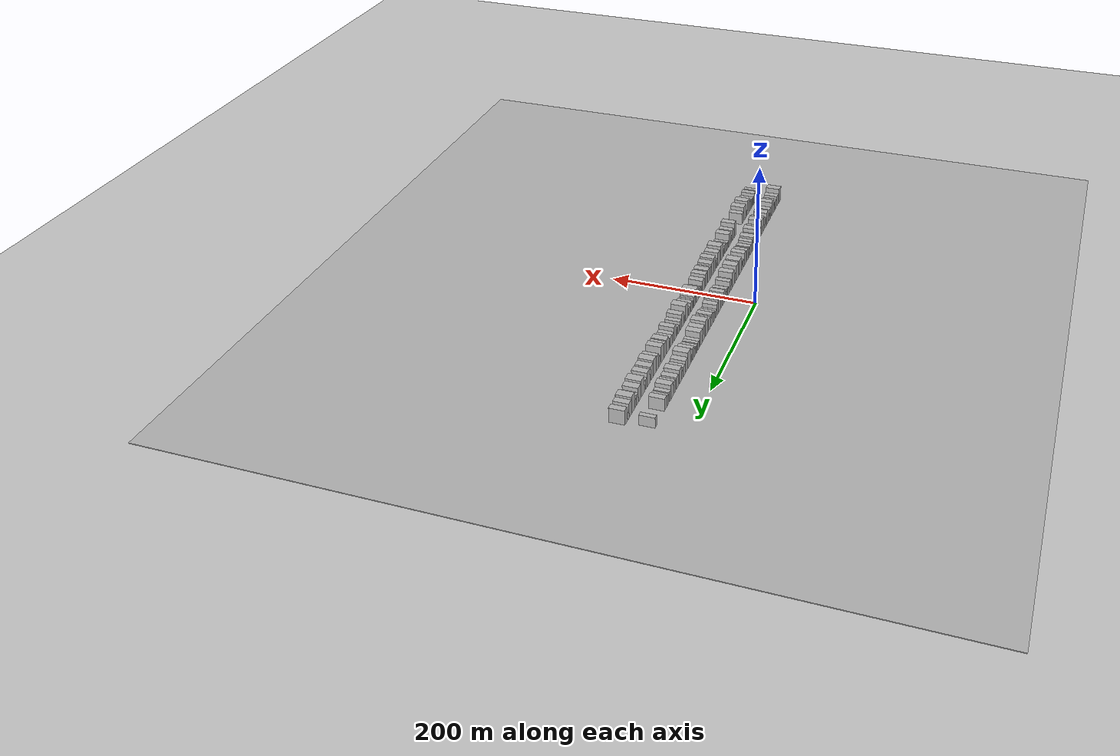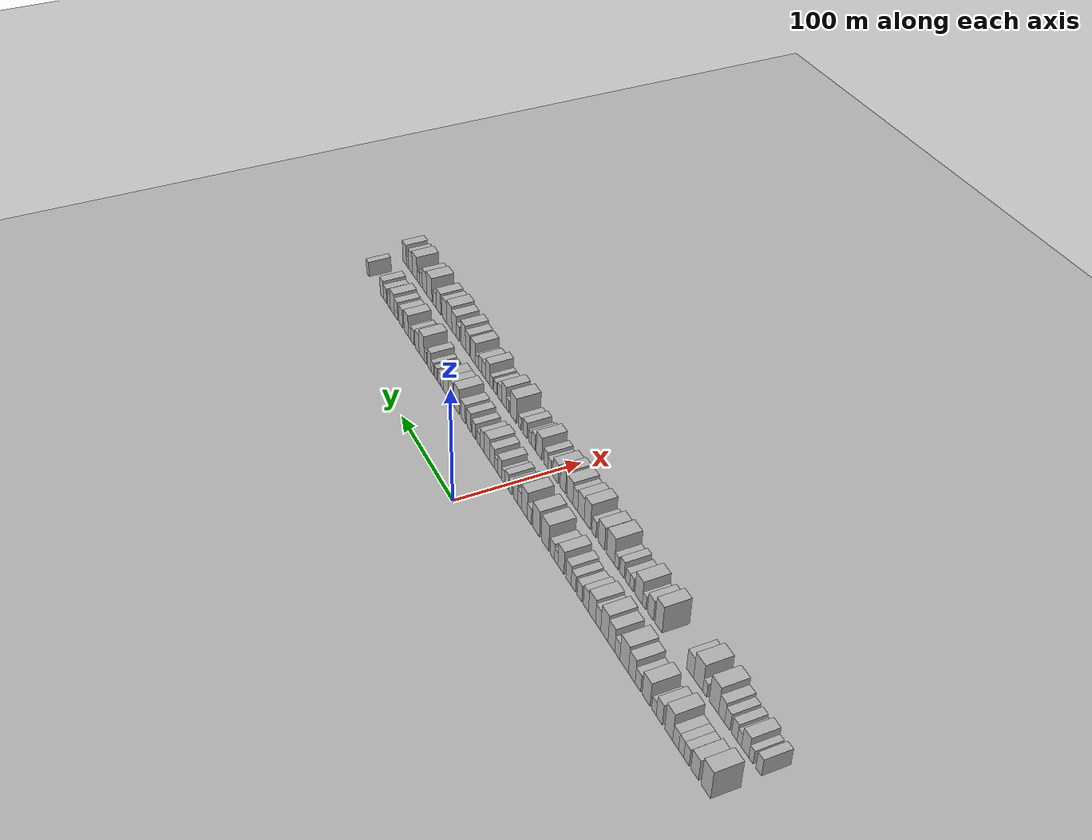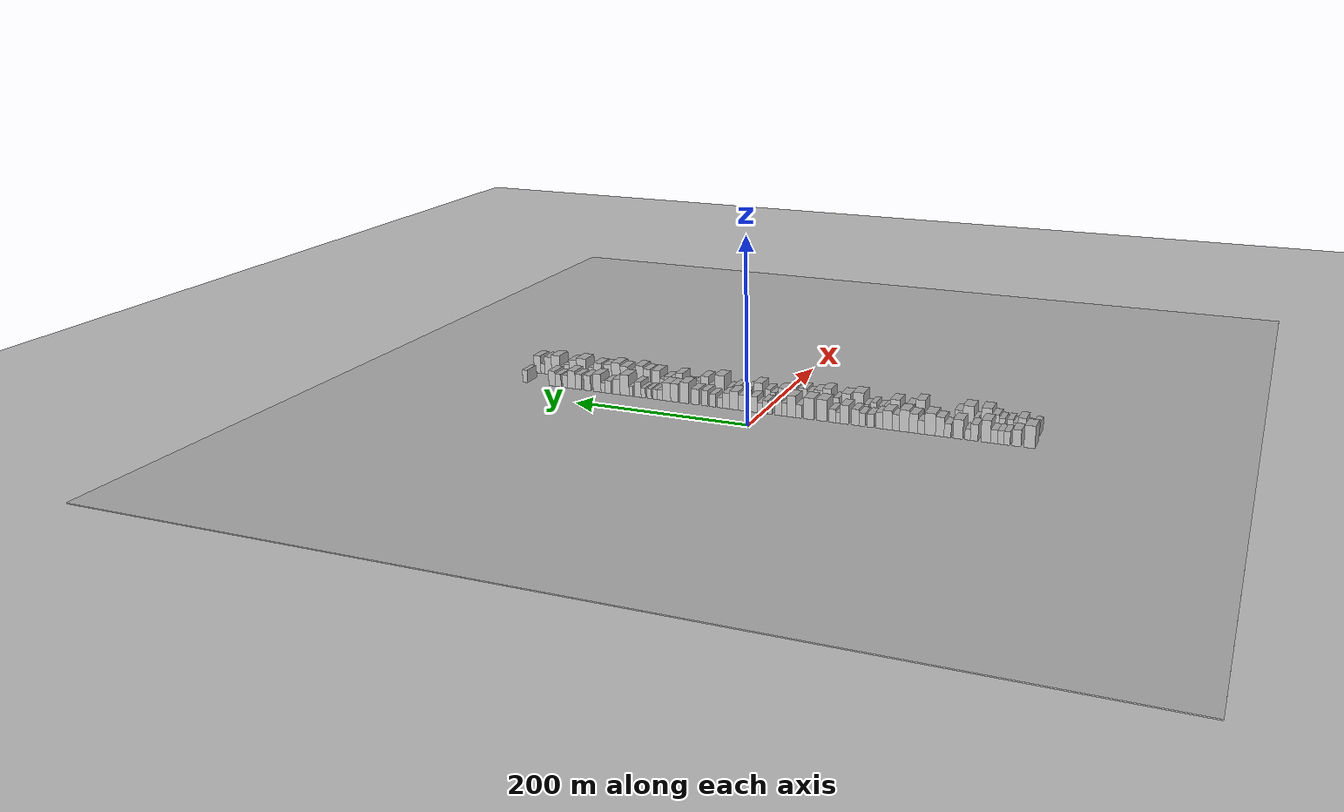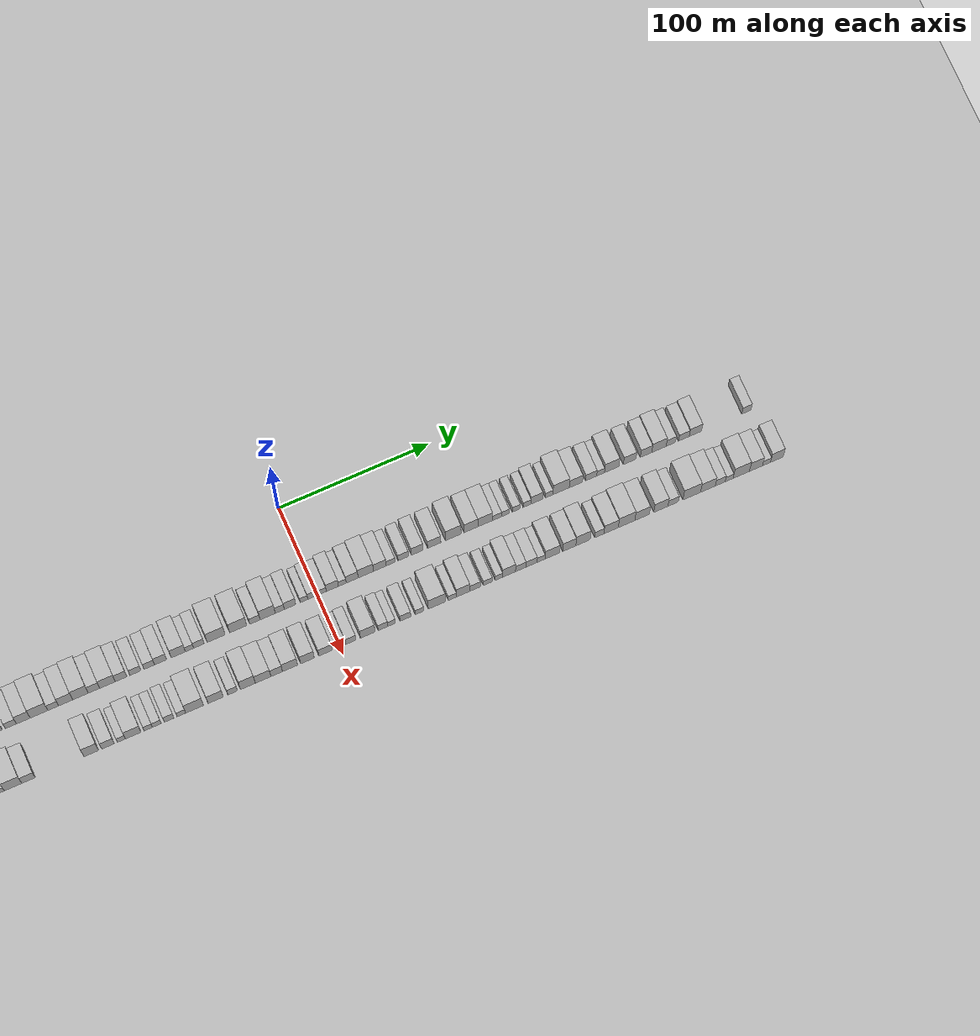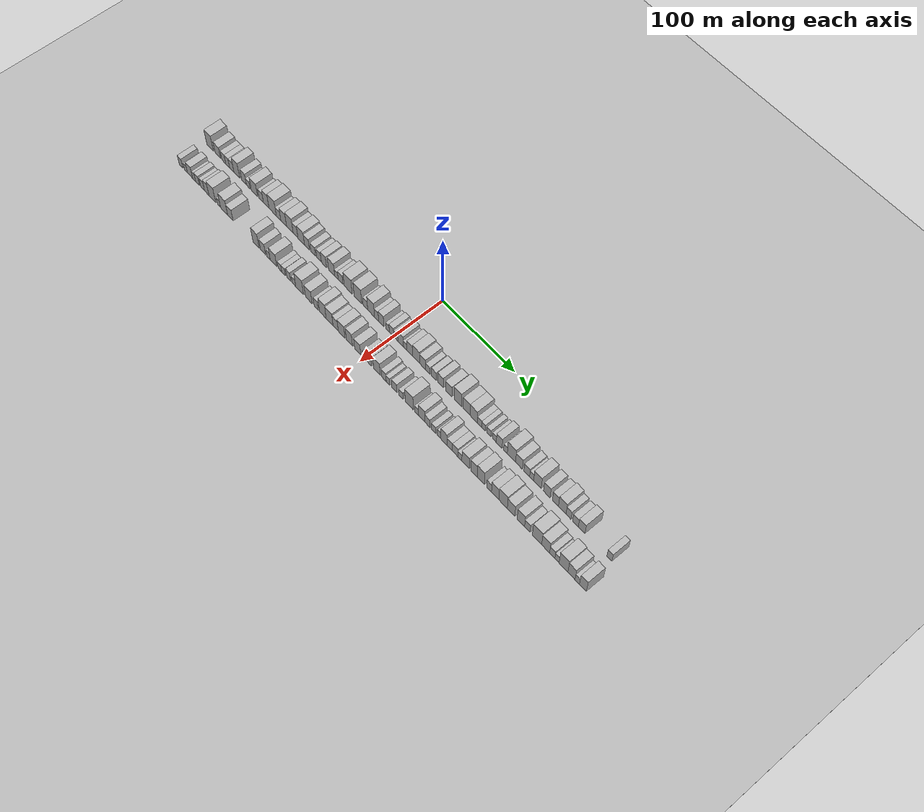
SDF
<?xml version="1.0" encoding="utf-8"?>

<sdf version="1.6">

   <world name="default">

      <gui fullscreen="0">

         <camera name="user_camera">

            <pose>-15 0 4.57585 0 0 0</pose>

            <view_controller>orbit</view_controller>

         </camera>

      </gui>

      <scene>

         <sky>

           <clouds>

             <speed>12</speed>

           </clouds>

         </sky>

         <ambient>0.4 0.4 0.4 1</ambient>

         <background>0.7 0.7 0.7 1</background>

         <shadows>1</shadows>

      </scene>

      <gravity>0 0 -9.8066</gravity>

      <magnetic_field>6e-06 2.3e-05 -4.2e-05</magnetic_field>

      <physics default="0" name="default_physics" type="ode">

         <ode>

            <solver>

               <type>quick</type>

               <iters>10</iters>

               <sor>1.0</sor>

               <use_dynamic_moi_rescaling>0</use_dynamic_moi_rescaling>

            </solver>

            <constraints>

               <cfm>0</cfm>

               <erp>0.2</erp>

               <contact_max_correcting_vel>100</contact_max_correcting_vel>

               <contact_surface_layer>0.001</contact_surface_layer>

            </constraints>

         </ode>

         <max_step_size>0.004</max_step_size>

         <real_time_factor>1</real_time_factor>

         <real_time_update_rate>250</real_time_update_rate>

      </physics>

      <light name="sun" type="directional">

         <cast_shadows>1</cast_shadows>

         <pose>0 0 10 0 0 0</pose>

         <diffuse>0.8 0.8 0.8 1</diffuse>

         <specular>0.2 0.2 0.2 1</specular>

         <attenuation>

            <range>1000</range>

            <constant>0.9</constant>

            <linear>0.01</linear>

            <quadratic>0.001</quadratic>

         </attenuation>

         <direction>-0.5 0.1 -0.9</direction>

      </light>

      <include>

         <name>ground_plane_1</name>

         <uri>model://HANNAS_ground_plane</uri>

         <pose>0 0 0  0 0 0</pose>

      </include>

      <include>

         <name>ground_plane_2</name>

         <uri>model://HANNAS_ground_plane</uri>

         <pose>100 0 0  0 0 0</pose>

      </include>

      <model name="building_1">

         <static>1</static>

         <pose frame="">50.0000 -284.5758 0 0.000000 0.000000 0.000000</pose>

         <link name="link">

            <pose frame="">0 0 12.00 0 0 0</pose>

            <collision name="collision">

               <geometry>

                  <box>

                     <size>20.0000 10.8484 24.0000</size>

                  </box>

               </geometry>

               <max_contacts>10</max_contacts>

               <surface>

                  <contact>

                     <ode/>

                  </contact>

                  <bounce/>

                  <friction>

                     <torsional>

                        <ode/>

                     </torsional>

                     <ode/>

                  </friction>

               </surface>

            </collision>

            <visual name="visual">

               <cast_shadows>0</cast_shadows>

               <geometry>

                  <box>

                     <size>20.0000 10.8484 24.0000</size>

                  </box>

               </geometry>

               <material>

                  <script>

                     <uri>model://HANNAS_wall/materials/scripts</uri>

                     <uri>model://HANNAS_wall/materials/textures</uri>

                     <name>vrc/HANNAS_wall</name>

                  </script>

               </material>

            </visual>

            <self_collide>0</self_collide>

            <enable_wind>0</enable_wind>

            <kinematic>0</kinematic>

         </link>

      </model>

      <model name="building_2">

         <static>1</static>

         <pose frame="">50.0000 -271.6562 0 0.000000 0.000000 0.000000</pose>

         <link name="link">

            <pose frame="">0 0 9.00 0 0 0</pose>

            <collision name="collision">

               <geometry>

                  <box>

                     <size>20.0000 8.9907 18.0000</size>

                  </box>

               </geometry>

               <max_contacts>10</max_contacts>

               <surface>

                  <contact>

                     <ode/>

                  </contact>

                  <bounce/>

                  <friction>

                     <torsional>

                        <ode/>

                     </torsional>

                     <ode/>

                  </friction>

               </surface>

            </collision>

            <visual name="visual">

               <cast_shadows>0</cast_shadows>

               <geometry>

                  <box>

                     <size>20.0000 8.9907 18.0000</size>

                  </box>

               </geometry>

               <material>

                  <script>

                     <uri>model://HANNAS_wall/materials/scripts</uri>

                     <uri>model://HANNAS_wall/materials/textures</uri>

                     <name>vrc/HANNAS_wall</name>

                  </script>

               </material>

            </visual>

            <self_collide>0</self_collide>

            <enable_wind>0</enable_wind>

            <kinematic>0</kinematic>

         </link>

      </model>

      <model name="building_3">

         <static>1</static>

         <pose frame="">50.0000 -261.9601 0 0.000000 0.000000 0.000000</pose>

         <link name="link">

            <pose frame="">0 0 7.50 0 0 0</pose>

            <collision name="collision">

               <geometry>

                  <box>

                     <size>20.0000 6.4016 15.0000</size>

                  </box>

               </geometry>

               <max_contacts>10</max_contacts>

               <surface>

                  <contact>

                     <ode/>

                  </contact>

                  <bounce/>

                  <friction>

                     <torsional>

                        <ode/>

                     </torsional>

                     <ode/>

                  </friction>

               </surface>

            </collision>

            <visual name="visual">

               <cast_shadows>0</cast_shadows>

               <geometry>

                  <box>

                     <size>20.0000 6.4016 15.0000</size>

                  </box>

               </geometry>

               <material>

                  <script>

                     <uri>model://HANNAS_wall/materials/scripts</uri>

                     <uri>model://HANNAS_wall/materials/textures</uri>

                     <name>vrc/HANNAS_wall</name>

                  </script>

               </material>

            </visual>

            <self_collide>0</self_collide>

            <enable_wind>0</enable_wind>

            <kinematic>0</kinematic>

         </link>

      </model>

      <model name="building_4">

         <static>1</static>

         <pose frame="">50.0000 -255.6335 0 0.000000 0.000000 0.000000</pose>

         <link name="link">

            <pose frame="">0 0 7.50 0 0 0</pose>

            <collision name="collision">

               <geometry>

                  <box>

                     <size>20.0000 6.2517 15.0000</size>

                  </box>

               </geometry>

               <max_contacts>10</max_contacts>

               <surface>

                  <contact>

                     <ode/>

                  </contact>

                  <bounce/>

                  <friction>

                     <torsional>

                        <ode/>

                     </torsional>

                     <ode/>

                  </friction>

               </surface>

            </collision>

            <visual name="visual">

               <cast_shadows>0</cast_shadows>

               <geometry>

                  <box>

                     <size>20.0000 6.2517 15.0000</size>

                  </box>

               </geometry>

               <material>

                  <script>

                     <uri>model://HANNAS_wall/materials/scripts</uri>

                     <uri>model://HANNAS_wall/materials/textures</uri>

                     <name>vrc/HANNAS_wall</name>

                  </script>

               </material>

            </visual>

            <self_collide>0</self_collide>

            <enable_wind>0</enable_wind>

            <kinematic>0</kinematic>

         </link>

      </model>

      <model name="building_5">

         <static>1</static>

         <pose frame="">50.0000 -248.9060 0 0.000000 0.000000 0.000000</pose>

         <link name="link">

            <pose frame="">0 0 7.50 0 0 0</pose>

            <collision name="collision">

               <geometry>

                  <box>

                     <size>20.0000 7.2034 15.0000</size>

                  </box>

               </geometry>

               <max_contacts>10</max_contacts>

               <surface>

                  <contact>

                     <ode/>

                  </contact>

                  <bounce/>

                  <friction>

                     <torsional>

                        <ode/>

                     </torsional>

                     <ode/>

                  </friction>

               </surface>

            </collision>

            <visual name="visual">

               <cast_shadows>0</cast_shadows>

               <geometry>

                  <box>

                     <size>20.0000 7.2034 15.0000</size>

                  </box>

               </geometry>

               <material>

                  <script>

                     <uri>model://HANNAS_wall/materials/scripts</uri>

                     <uri>model://HANNAS_wall/materials/textures</uri>

                     <name>vrc/HANNAS_wall</name>

                  </script>

               </material>

            </visual>

            <self_collide>0</self_collide>

            <enable_wind>0</enable_wind>

            <kinematic>0</kinematic>

         </link>

      </model>

      <model name="building_6">

         <static>1</static>

         <pose frame="">50.0000 -240.4666 0 0.000000 0.000000 0.000000</pose>

         <link name="link">

            <pose frame="">0 0 12.00 0 0 0</pose>

            <collision name="collision">

               <geometry>

                  <box>

                     <size>20.0000 9.6754 24.0000</size>

                  </box>

               </geometry>

               <max_contacts>10</max_contacts>

               <surface>

                  <contact>

                     <ode/>

                  </contact>

                  <bounce/>

                  <friction>

                     <torsional>

                        <ode/>

                     </torsional>

                     <ode/>

                  </friction>

               </surface>

            </collision>

            <visual name="visual">

               <cast_shadows>0</cast_shadows>

               <geometry>

                  <box>

                     <size>20.0000 9.6754 24.0000</size>

                  </box>

               </geometry>

               <material>

                  <script>

                     <uri>model://HANNAS_wall/materials/scripts</uri>

                     <uri>model://HANNAS_wall/materials/textures</uri>

                     <name>vrc/HANNAS_wall</name>

                  </script>

               </material>

            </visual>

            <self_collide>0</self_collide>

            <enable_wind>0</enable_wind>

            <kinematic>0</kinematic>

         </link>

      </model>

      <model name="building_7">

         <static>1</static>

         <pose frame="">50.0000 -228.7247 0 0.000000 0.000000 0.000000</pose>

         <link name="link">

            <pose frame="">0 0 9.00 0 0 0</pose>

            <collision name="collision">

               <geometry>

                  <box>

                     <size>20.0000 7.8084 18.0000</size>

                  </box>

               </geometry>

               <max_contacts>10</max_contacts>

               <surface>

                  <contact>

                     <ode/>

                  </contact>

                  <bounce/>

                  <friction>

                     <torsional>

                        <ode/>

                     </torsional>

                     <ode/>

                  </friction>

               </surface>

            </collision>

            <visual name="visual">

               <cast_shadows>0</cast_shadows>

               <geometry>

                  <box>

                     <size>20.0000 7.8084 18.0000</size>

                  </box>

               </geometry>

               <material>

                  <script>

                     <uri>model://HANNAS_wall/materials/scripts</uri>

                     <uri>model://HANNAS_wall/materials/textures</uri>

                     <name>vrc/HANNAS_wall</name>

                  </script>

               </material>

            </visual>

            <self_collide>0</self_collide>

            <enable_wind>0</enable_wind>

            <kinematic>0</kinematic>

         </link>

      </model>

      <model name="building_8">

         <static>1</static>

         <pose frame="">50.0000 -221.9876 0 0.000000 0.000000 0.000000</pose>

         <link name="link">

            <pose frame="">0 0 6.00 0 0 0</pose>

            <collision name="collision">

               <geometry>

                  <box>

                     <size>20.0000 5.6657 12.0000</size>

                  </box>

               </geometry>

               <max_contacts>10</max_contacts>

               <surface>

                  <contact>

                     <ode/>

                  </contact>

                  <bounce/>

                  <friction>

                     <torsional>

                        <ode/>

                     </torsional>

                     <ode/>

                  </friction>

               </surface>

            </collision>

            <visual name="visual">

               <cast_shadows>0</cast_shadows>

               <geometry>

                  <box>

                     <size>20.0000 5.6657 12.0000</size>

                  </box>

               </geometry>

               <material>

                  <script>

                     <uri>model://HANNAS_wall/materials/scripts</uri>

                     <uri>model://HANNAS_wall/materials/textures</uri>

                     <name>vrc/HANNAS_wall</name>

                  </script>

               </material>

            </visual>

            <self_collide>0</self_collide>

            <enable_wind>0</enable_wind>

            <kinematic>0</kinematic>

         </link>

      </model>

      <model name="building_9">

         <static>1</static>

         <pose frame="">50.0000 -212.0377 0 0.000000 0.000000 0.000000</pose>

         <link name="link">

            <pose frame="">0 0 10.50 0 0 0</pose>

            <collision name="collision">

               <geometry>

                  <box>

                     <size>20.0000 10.2342 21.0000</size>

                  </box>

               </geometry>

               <max_contacts>10</max_contacts>

               <surface>

                  <contact>

                     <ode/>

                  </contact>

                  <bounce/>

                  <friction>

                     <torsional>

                        <ode/>

                     </torsional>

                     <ode/>

                  </friction>

               </surface>

            </collision>

            <visual name="visual">

               <cast_shadows>0</cast_shadows>

               <geometry>

                  <box>

                     <size>20.0000 10.2342 21.0000</size>

                  </box>

               </geometry>

               <material>

                  <script>

                     <uri>model://HANNAS_wall/materials/scripts</uri>

                     <uri>model://HANNAS_wall/materials/textures</uri>

                     <name>vrc/HANNAS_wall</name>

                  </script>

               </material>

            </visual>

            <self_collide>0</self_collide>

            <enable_wind>0</enable_wind>

            <kinematic>0</kinematic>

         </link>

      </model>

      <model name="building_10">

         <static>1</static>

         <pose frame="">50.0000 -201.2680 0 0.000000 0.000000 0.000000</pose>

         <link name="link">

            <pose frame="">0 0 7.50 0 0 0</pose>

            <collision name="collision">

               <geometry>

                  <box>

                     <size>20.0000 7.3052 15.0000</size>

                  </box>

               </geometry>

               <max_contacts>10</max_contacts>

               <surface>

                  <contact>

                     <ode/>

                  </contact>

                  <bounce/>

                  <friction>

                     <torsional>

                        <ode/>

                     </torsional>

                     <ode/>

                  </friction>

               </surface>

            </collision>

            <visual name="visual">

               <cast_shadows>0</cast_shadows>

               <geometry>

                  <box>

                     <size>20.0000 7.3052 15.0000</size>

                  </box>

               </geometry>

               <material>

                  <script>

                     <uri>model://HANNAS_wall/materials/scripts</uri>

                     <uri>model://HANNAS_wall/materials/textures</uri>

                     <name>vrc/HANNAS_wall</name>

                  </script>

               </material>

            </visual>

            <self_collide>0</self_collide>

            <enable_wind>0</enable_wind>

            <kinematic>0</kinematic>

         </link>

      </model>

      <model name="building_11">

         <static>1</static>

         <pose frame="">50.0000 -193.1629 0 0.000000 0.000000 0.000000</pose>

         <link name="link">

            <pose frame="">0 0 10.50 0 0 0</pose>

            <collision name="collision">

               <geometry>

                  <box>

                     <size>20.0000 8.9050 21.0000</size>

                  </box>

               </geometry>

               <max_contacts>10</max_contacts>

               <surface>

                  <contact>

                     <ode/>

                  </contact>

                  <bounce/>

                  <friction>

                     <torsional>

                        <ode/>

                     </torsional>

                     <ode/>

                  </friction>

               </surface>

            </collision>

            <visual name="visual">

               <cast_shadows>0</cast_shadows>

               <geometry>

                  <box>

                     <size>20.0000 8.9050 21.0000</size>

                  </box>

               </geometry>

               <material>

                  <script>

                     <uri>model://HANNAS_wall/materials/scripts</uri>

                     <uri>model://HANNAS_wall/materials/textures</uri>

                     <name>vrc/HANNAS_wall</name>

                  </script>

               </material>

            </visual>

            <self_collide>0</self_collide>

            <enable_wind>0</enable_wind>

            <kinematic>0</kinematic>

         </link>

      </model>

      <model name="building_12">

         <static>1</static>

         <pose frame="">50.0000 -182.9442 0 0.000000 0.000000 0.000000</pose>

         <link name="link">

            <pose frame="">0 0 12.00 0 0 0</pose>

            <collision name="collision">

               <geometry>

                  <box>

                     <size>20.0000 11.5325 24.0000</size>

                  </box>

               </geometry>

               <max_contacts>10</max_contacts>

               <surface>

                  <contact>

                     <ode/>

                  </contact>

                  <bounce/>

                  <friction>

                     <torsional>

                        <ode/>

                     </torsional>

                     <ode/>

                  </friction>

               </surface>

            </collision>

            <visual name="visual">

               <cast_shadows>0</cast_shadows>

               <geometry>

                  <box>

                     <size>20.0000 11.5325 24.0000</size>

                  </box>

               </geometry>

               <material>

                  <script>

                     <uri>model://HANNAS_wall/materials/scripts</uri>

                     <uri>model://HANNAS_wall/materials/textures</uri>

                     <name>vrc/HANNAS_wall</name>

                  </script>

               </material>

            </visual>

            <self_collide>0</self_collide>

            <enable_wind>0</enable_wind>

            <kinematic>0</kinematic>

         </link>

      </model>

      <model name="building_13">

         <static>1</static>

         <pose frame="">50.0000 -173.6545 0 0.000000 0.000000 0.000000</pose>

         <link name="link">

            <pose frame="">0 0 7.50 0 0 0</pose>

            <collision name="collision">

               <geometry>

                  <box>

                     <size>20.0000 7.0468 15.0000</size>

                  </box>

               </geometry>

               <max_contacts>10</max_contacts>

               <surface>

                  <contact>

                     <ode/>

                  </contact>

                  <bounce/>

                  <friction>

                     <torsional>

                        <ode/>

                     </torsional>

                     <ode/>

                  </friction>

               </surface>

            </collision>

            <visual name="visual">

               <cast_shadows>0</cast_shadows>

               <geometry>

                  <box>

                     <size>20.0000 7.0468 15.0000</size>

                  </box>

               </geometry>

               <material>

                  <script>

                     <uri>model://HANNAS_wall/materials/scripts</uri>

                     <uri>model://HANNAS_wall/materials/textures</uri>

                     <name>vrc/HANNAS_wall</name>

                  </script>

               </material>

            </visual>

            <self_collide>0</self_collide>

            <enable_wind>0</enable_wind>

            <kinematic>0</kinematic>

         </link>

      </model>

      <model name="building_14">

         <static>1</static>

         <pose frame="">50.0000 -165.5203 0 0.000000 0.000000 0.000000</pose>

         <link name="link">

            <pose frame="">0 0 10.50 0 0 0</pose>

            <collision name="collision">

               <geometry>

                  <box>

                     <size>20.0000 9.2216 21.0000</size>

                  </box>

               </geometry>

               <max_contacts>10</max_contacts>

               <surface>

                  <contact>

                     <ode/>

                  </contact>

                  <bounce/>

                  <friction>

                     <torsional>

                        <ode/>

                     </torsional>

                     <ode/>

                  </friction>

               </surface>

            </collision>

            <visual name="visual">

               <cast_shadows>0</cast_shadows>

               <geometry>

                  <box>

                     <size>20.0000 9.2216 21.0000</size>

                  </box>

               </geometry>

               <material>

                  <script>

                     <uri>model://HANNAS_wall/materials/scripts</uri>

                     <uri>model://HANNAS_wall/materials/textures</uri>

                     <name>vrc/HANNAS_wall</name>

                  </script>

               </material>

            </visual>

            <self_collide>0</self_collide>

            <enable_wind>0</enable_wind>

            <kinematic>0</kinematic>

         </link>

      </model>

      <model name="building_15">

         <static>1</static>

         <pose frame="">50.0000 -155.7967 0 0.000000 0.000000 0.000000</pose>

         <link name="link">

            <pose frame="">0 0 12.00 0 0 0</pose>

            <collision name="collision">

               <geometry>

                  <box>

                     <size>20.0000 10.2256 24.0000</size>

                  </box>

               </geometry>

               <max_contacts>10</max_contacts>

               <surface>

                  <contact>

                     <ode/>

                  </contact>

                  <bounce/>

                  <friction>

                     <torsional>

                        <ode/>

                     </torsional>

                     <ode/>

                  </friction>

               </surface>

            </collision>

            <visual name="visual">

               <cast_shadows>0</cast_shadows>

               <geometry>

                  <box>

                     <size>20.0000 10.2256 24.0000</size>

                  </box>

               </geometry>

               <material>

                  <script>

                     <uri>model://HANNAS_wall/materials/scripts</uri>

                     <uri>model://HANNAS_wall/materials/textures</uri>

                     <name>vrc/HANNAS_wall</name>

                  </script>

               </material>

            </visual>

            <self_collide>0</self_collide>

            <enable_wind>0</enable_wind>

            <kinematic>0</kinematic>

         </link>

      </model>

      <model name="building_16">

         <static>1</static>

         <pose frame="">50.0000 -146.9506 0 0.000000 0.000000 0.000000</pose>

         <link name="link">

            <pose frame="">0 0 9.00 0 0 0</pose>

            <collision name="collision">

               <geometry>

                  <box>

                     <size>20.0000 7.4665 18.0000</size>

                  </box>

               </geometry>

               <max_contacts>10</max_contacts>

               <surface>

                  <contact>

                     <ode/>

                  </contact>

                  <bounce/>

                  <friction>

                     <torsional>

                        <ode/>

                     </torsional>

                     <ode/>

                  </friction>

               </surface>

            </collision>

            <visual name="visual">

               <cast_shadows>0</cast_shadows>

               <geometry>

                  <box>

                     <size>20.0000 7.4665 18.0000</size>

                  </box>

               </geometry>

               <material>

                  <script>

                     <uri>model://HANNAS_wall/materials/scripts</uri>

                     <uri>model://HANNAS_wall/materials/textures</uri>

                     <name>vrc/HANNAS_wall</name>

                  </script>

               </material>

            </visual>

            <self_collide>0</self_collide>

            <enable_wind>0</enable_wind>

            <kinematic>0</kinematic>

         </link>

      </model>

      <model name="building_17">

         <static>1</static>

         <pose frame="">50.0000 -138.1325 0 0.000000 0.000000 0.000000</pose>

         <link name="link">

            <pose frame="">0 0 10.50 0 0 0</pose>

            <collision name="collision">

               <geometry>

                  <box>

                     <size>20.0000 10.1697 21.0000</size>

                  </box>

               </geometry>

               <max_contacts>10</max_contacts>

               <surface>

                  <contact>

                     <ode/>

                  </contact>

                  <bounce/>

                  <friction>

                     <torsional>

                        <ode/>

                     </torsional>

                     <ode/>

                  </friction>

               </surface>

            </collision>

            <visual name="visual">

               <cast_shadows>0</cast_shadows>

               <geometry>

                  <box>

                     <size>20.0000 10.1697 21.0000</size>

                  </box>

               </geometry>

               <material>

                  <script>

                     <uri>model://HANNAS_wall/materials/scripts</uri>

                     <uri>model://HANNAS_wall/materials/textures</uri>

                     <name>vrc/HANNAS_wall</name>

                  </script>

               </material>

            </visual>

            <self_collide>0</self_collide>

            <enable_wind>0</enable_wind>

            <kinematic>0</kinematic>

         </link>

      </model>

      <model name="building_18">

         <static>1</static>

         <pose frame="">50.0000 -129.2719 0 0.000000 0.000000 0.000000</pose>

         <link name="link">

            <pose frame="">0 0 9.00 0 0 0</pose>

            <collision name="collision">

               <geometry>

                  <box>

                     <size>20.0000 7.5515 18.0000</size>

                  </box>

               </geometry>

               <max_contacts>10</max_contacts>

               <surface>

                  <contact>

                     <ode/>

                  </contact>

                  <bounce/>

                  <friction>

                     <torsional>

                        <ode/>

                     </torsional>

                     <ode/>

                  </friction>

               </surface>

            </collision>

            <visual name="visual">

               <cast_shadows>0</cast_shadows>

               <geometry>

                  <box>

                     <size>20.0000 7.5515 18.0000</size>

                  </box>

               </geometry>

               <material>

                  <script>

                     <uri>model://HANNAS_wall/materials/scripts</uri>

                     <uri>model://HANNAS_wall/materials/textures</uri>

                     <name>vrc/HANNAS_wall</name>

                  </script>

               </material>

            </visual>

            <self_collide>0</self_collide>

            <enable_wind>0</enable_wind>

            <kinematic>0</kinematic>

         </link>

      </model>

      <model name="building_19">

         <static>1</static>

         <pose frame="">50.0000 -119.8560 0 0.000000 0.000000 0.000000</pose>

         <link name="link">

            <pose frame="">0 0 7.50 0 0 0</pose>

            <collision name="collision">

               <geometry>

                  <box>

                     <size>20.0000 7.2804 15.0000</size>

                  </box>

               </geometry>

               <max_contacts>10</max_contacts>

               <surface>

                  <contact>

                     <ode/>

                  </contact>

                  <bounce/>

                  <friction>

                     <torsional>

                        <ode/>

                     </torsional>

                     <ode/>

                  </friction>

               </surface>

            </collision>

            <visual name="visual">

               <cast_shadows>0</cast_shadows>

               <geometry>

                  <box>

                     <size>20.0000 7.2804 15.0000</size>

                  </box>

               </geometry>

               <material>

                  <script>

                     <uri>model://HANNAS_wall/materials/scripts</uri>

                     <uri>model://HANNAS_wall/materials/textures</uri>

                     <name>vrc/HANNAS_wall</name>

                  </script>

               </material>

            </visual>

            <self_collide>0</self_collide>

            <enable_wind>0</enable_wind>

            <kinematic>0</kinematic>

         </link>

      </model>

      <model name="building_20">

         <static>1</static>

         <pose frame="">50.0000 -110.7603 0 0.000000 0.000000 0.000000</pose>

         <link name="link">

            <pose frame="">0 0 7.50 0 0 0</pose>

            <collision name="collision">

               <geometry>

                  <box>

                     <size>20.0000 6.9111 15.0000</size>

                  </box>

               </geometry>

               <max_contacts>10</max_contacts>

               <surface>

                  <contact>

                     <ode/>

                  </contact>

                  <bounce/>

                  <friction>

                     <torsional>

                        <ode/>

                     </torsional>

                     <ode/>

                  </friction>

               </surface>

            </collision>

            <visual name="visual">

               <cast_shadows>0</cast_shadows>

               <geometry>

                  <box>

                     <size>20.0000 6.9111 15.0000</size>

                  </box>

               </geometry>

               <material>

                  <script>

                     <uri>model://HANNAS_wall/materials/scripts</uri>

                     <uri>model://HANNAS_wall/materials/textures</uri>

                     <name>vrc/HANNAS_wall</name>

                  </script>

               </material>

            </visual>

            <self_collide>0</self_collide>

            <enable_wind>0</enable_wind>

            <kinematic>0</kinematic>

         </link>

      </model>

      <model name="building_21">

         <static>1</static>

         <pose frame="">50.0000 -103.3472 0 0.000000 0.000000 0.000000</pose>

         <link name="link">

            <pose frame="">0 0 9.00 0 0 0</pose>

            <collision name="collision">

               <geometry>

                  <box>

                     <size>20.0000 7.9150 18.0000</size>

                  </box>

               </geometry>

               <max_contacts>10</max_contacts>

               <surface>

                  <contact>

                     <ode/>

                  </contact>

                  <bounce/>

                  <friction>

                     <torsional>

                        <ode/>

                     </torsional>

                     <ode/>

                  </friction>

               </surface>

            </collision>

            <visual name="visual">

               <cast_shadows>0</cast_shadows>

               <geometry>

                  <box>

                     <size>20.0000 7.9150 18.0000</size>

                  </box>

               </geometry>

               <material>

                  <script>

                     <uri>model://HANNAS_wall/materials/scripts</uri>

                     <uri>model://HANNAS_wall/materials/textures</uri>

                     <name>vrc/HANNAS_wall</name>

                  </script>

               </material>

            </visual>

            <self_collide>0</self_collide>

            <enable_wind>0</enable_wind>

            <kinematic>0</kinematic>

         </link>

      </model>

      <model name="building_22">

         <static>1</static>

         <pose frame="">50.0000 -91.7295 0 0.000000 0.000000 0.000000</pose>

         <link name="link">

            <pose frame="">0 0 10.50 0 0 0</pose>

            <collision name="collision">

               <geometry>

                  <box>

                     <size>20.0000 9.3206 21.0000</size>

                  </box>

               </geometry>

               <max_contacts>10</max_contacts>

               <surface>

                  <contact>

                     <ode/>

                  </contact>

                  <bounce/>

                  <friction>

                     <torsional>

                        <ode/>

                     </torsional>

                     <ode/>

                  </friction>

               </surface>

            </collision>

            <visual name="visual">

               <cast_shadows>0</cast_shadows>

               <geometry>

                  <box>

                     <size>20.0000 9.3206 21.0000</size>

                  </box>

               </geometry>

               <material>

                  <script>

                     <uri>model://HANNAS_wall/materials/scripts</uri>

                     <uri>model://HANNAS_wall/materials/textures</uri>

                     <name>vrc/HANNAS_wall</name>

                  </script>

               </material>

            </visual>

            <self_collide>0</self_collide>

            <enable_wind>0</enable_wind>

            <kinematic>0</kinematic>

         </link>

      </model>

      <model name="building_23">

         <static>1</static>

         <pose frame="">50.0000 -84.3872 0 0.000000 0.000000 0.000000</pose>

         <link name="link">

            <pose frame="">0 0 6.00 0 0 0</pose>

            <collision name="collision">

               <geometry>

                  <box>

                     <size>20.0000 5.3639 12.0000</size>

                  </box>

               </geometry>

               <max_contacts>10</max_contacts>

               <surface>

                  <contact>

                     <ode/>

                  </contact>

                  <bounce/>

                  <friction>

                     <torsional>

                        <ode/>

                     </torsional>

                     <ode/>

                  </friction>

               </surface>

            </collision>

            <visual name="visual">

               <cast_shadows>0</cast_shadows>

               <geometry>

                  <box>

                     <size>20.0000 5.3639 12.0000</size>

                  </box>

               </geometry>

               <material>

                  <script>

                     <uri>model://HANNAS_wall/materials/scripts</uri>

                     <uri>model://HANNAS_wall/materials/textures</uri>

                     <name>vrc/HANNAS_wall</name>

                  </script>

               </material>

            </visual>

            <self_collide>0</self_collide>

            <enable_wind>0</enable_wind>

            <kinematic>0</kinematic>

         </link>

      </model>

      <model name="building_24">

         <static>1</static>

         <pose frame="">50.0000 -78.2163 0 0.000000 0.000000 0.000000</pose>

         <link name="link">

            <pose frame="">0 0 7.50 0 0 0</pose>

            <collision name="collision">

               <geometry>

                  <box>

                     <size>20.0000 6.9779 15.0000</size>

                  </box>

               </geometry>

               <max_contacts>10</max_contacts>

               <surface>

                  <contact>

                     <ode/>

                  </contact>

                  <bounce/>

                  <friction>

                     <torsional>

                        <ode/>

                     </torsional>

                     <ode/>

                  </friction>

               </surface>

            </collision>

            <visual name="visual">

               <cast_shadows>0</cast_shadows>

               <geometry>

                  <box>

                     <size>20.0000 6.9779 15.0000</size>

                  </box>

               </geometry>

               <material>

                  <script>

                     <uri>model://HANNAS_wall/materials/scripts</uri>

                     <uri>model://HANNAS_wall/materials/textures</uri>

                     <name>vrc/HANNAS_wall</name>

                  </script>

               </material>

            </visual>

            <self_collide>0</self_collide>

            <enable_wind>0</enable_wind>

            <kinematic>0</kinematic>

         </link>

      </model>

      <model name="building_25">

         <static>1</static>

         <pose frame="">50.0000 -66.8264 0 0.000000 0.000000 0.000000</pose>

         <link name="link">

            <pose frame="">0 0 12.00 0 0 0</pose>

            <collision name="collision">

               <geometry>

                  <box>

                     <size>20.0000 11.8019 24.0000</size>

                  </box>

               </geometry>

               <max_contacts>10</max_contacts>

               <surface>

                  <contact>

                     <ode/>

                  </contact>

                  <bounce/>

                  <friction>

                     <torsional>

                        <ode/>

                     </torsional>

                     <ode/>

                  </friction>

               </surface>

            </collision>

            <visual name="visual">

               <cast_shadows>0</cast_shadows>

               <geometry>

                  <box>

                     <size>20.0000 11.8019 24.0000</size>

                  </box>

               </geometry>

               <material>

                  <script>

                     <uri>model://HANNAS_wall/materials/scripts</uri>

                     <uri>model://HANNAS_wall/materials/textures</uri>

                     <name>vrc/HANNAS_wall</name>

                  </script>

               </material>

            </visual>

            <self_collide>0</self_collide>

            <enable_wind>0</enable_wind>

            <kinematic>0</kinematic>

         </link>

      </model>

      <model name="building_26">

         <static>1</static>

         <pose frame="">50.0000 -52.2825 0 0.000000 0.000000 0.000000</pose>

         <link name="link">

            <pose frame="">0 0 12.00 0 0 0</pose>

            <collision name="collision">

               <geometry>

                  <box>

                     <size>20.0000 11.2858 24.0000</size>

                  </box>

               </geometry>

               <max_contacts>10</max_contacts>

               <surface>

                  <contact>

                     <ode/>

                  </contact>

                  <bounce/>

                  <friction>

                     <torsional>

                        <ode/>

                     </torsional>

                     <ode/>

                  </friction>

               </surface>

            </collision>

            <visual name="visual">

               <cast_shadows>0</cast_shadows>

               <geometry>

                  <box>

                     <size>20.0000 11.2858 24.0000</size>

                  </box>

               </geometry>

               <material>

                  <script>

                     <uri>model://HANNAS_wall/materials/scripts</uri>

                     <uri>model://HANNAS_wall/materials/textures</uri>

                     <name>vrc/HANNAS_wall</name>

                  </script>

               </material>

            </visual>

            <self_collide>0</self_collide>

            <enable_wind>0</enable_wind>

            <kinematic>0</kinematic>

         </link>

      </model>

      <model name="building_27">

         <static>1</static>

         <pose frame="">50.0000 -41.2421 0 0.000000 0.000000 0.000000</pose>

         <link name="link">

            <pose frame="">0 0 7.50 0 0 0</pose>

            <collision name="collision">

               <geometry>

                  <box>

                     <size>20.0000 6.7951 15.0000</size>

                  </box>

               </geometry>

               <max_contacts>10</max_contacts>

               <surface>

                  <contact>

                     <ode/>

                  </contact>

                  <bounce/>

                  <friction>

                     <torsional>

                        <ode/>

                     </torsional>

                     <ode/>

                  </friction>

               </surface>

            </collision>

            <visual name="visual">

               <cast_shadows>0</cast_shadows>

               <geometry>

                  <box>

                     <size>20.0000 6.7951 15.0000</size>

                  </box>

               </geometry>

               <material>

                  <script>

                     <uri>model://HANNAS_wall/materials/scripts</uri>

                     <uri>model://HANNAS_wall/materials/textures</uri>

                     <name>vrc/HANNAS_wall</name>

                  </script>

               </material>

            </visual>

            <self_collide>0</self_collide>

            <enable_wind>0</enable_wind>

            <kinematic>0</kinematic>

         </link>

      </model>

      <model name="building_28">

         <static>1</static>

         <pose frame="">50.0000 -32.8636 0 0.000000 0.000000 0.000000</pose>

         <link name="link">

            <pose frame="">0 0 12.00 0 0 0</pose>

            <collision name="collision">

               <geometry>

                  <box>

                     <size>20.0000 9.9619 24.0000</size>

                  </box>

               </geometry>

               <max_contacts>10</max_contacts>

               <surface>

                  <contact>

                     <ode/>

                  </contact>

                  <bounce/>

                  <friction>

                     <torsional>

                        <ode/>

                     </torsional>

                     <ode/>

                  </friction>

               </surface>

            </collision>

            <visual name="visual">

               <cast_shadows>0</cast_shadows>

               <geometry>

                  <box>

                     <size>20.0000 9.9619 24.0000</size>

                  </box>

               </geometry>

               <material>

                  <script>

                     <uri>model://HANNAS_wall/materials/scripts</uri>

                     <uri>model://HANNAS_wall/materials/textures</uri>

                     <name>vrc/HANNAS_wall</name>

                  </script>

               </material>

            </visual>

            <self_collide>0</self_collide>

            <enable_wind>0</enable_wind>

            <kinematic>0</kinematic>

         </link>

      </model>

      <model name="building_29">

         <static>1</static>

         <pose frame="">50.0000 -24.8612 0 0.000000 0.000000 0.000000</pose>

         <link name="link">

            <pose frame="">0 0 7.50 0 0 0</pose>

            <collision name="collision">

               <geometry>

                  <box>

                     <size>20.0000 6.0428 15.0000</size>

                  </box>

               </geometry>

               <max_contacts>10</max_contacts>

               <surface>

                  <contact>

                     <ode/>

                  </contact>

                  <bounce/>

                  <friction>

                     <torsional>

                        <ode/>

                     </torsional>

                     <ode/>

                  </friction>

               </surface>

            </collision>

            <visual name="visual">

               <cast_shadows>0</cast_shadows>

               <geometry>

                  <box>

                     <size>20.0000 6.0428 15.0000</size>

                  </box>

               </geometry>

               <material>

                  <script>

                     <uri>model://HANNAS_wall/materials/scripts</uri>

                     <uri>model://HANNAS_wall/materials/textures</uri>

                     <name>vrc/HANNAS_wall</name>

                  </script>

               </material>

            </visual>

            <self_collide>0</self_collide>

            <enable_wind>0</enable_wind>

            <kinematic>0</kinematic>

         </link>

      </model>

      <model name="building_30">

         <static>1</static>

         <pose frame="">50.0000 -18.0613 0 0.000000 0.000000 0.000000</pose>

         <link name="link">

            <pose frame="">0 0 9.00 0 0 0</pose>

            <collision name="collision">

               <geometry>

                  <box>

                     <size>20.0000 7.5571 18.0000</size>

                  </box>

               </geometry>

               <max_contacts>10</max_contacts>

               <surface>

                  <contact>

                     <ode/>

                  </contact>

                  <bounce/>

                  <friction>

                     <torsional>

                        <ode/>

                     </torsional>

                     <ode/>

                  </friction>

               </surface>

            </collision>

            <visual name="visual">

               <cast_shadows>0</cast_shadows>

               <geometry>

                  <box>

                     <size>20.0000 7.5571 18.0000</size>

                  </box>

               </geometry>

               <material>

                  <script>

                     <uri>model://HANNAS_wall/materials/scripts</uri>

                     <uri>model://HANNAS_wall/materials/textures</uri>

                     <name>vrc/HANNAS_wall</name>

                  </script>

               </material>

            </visual>

            <self_collide>0</self_collide>

            <enable_wind>0</enable_wind>

            <kinematic>0</kinematic>

         </link>

      </model>

      <model name="building_31">

         <static>1</static>

         <pose frame="">50.0000 -8.8151 0 0.000000 0.000000 0.000000</pose>

         <link name="link">

            <pose frame="">0 0 6.00 0 0 0</pose>

            <collision name="collision">

               <geometry>

                  <box>

                     <size>20.0000 4.9353 12.0000</size>

                  </box>

               </geometry>

               <max_contacts>10</max_contacts>

               <surface>

                  <contact>

                     <ode/>

                  </contact>

                  <bounce/>

                  <friction>

                     <torsional>

                        <ode/>

                     </torsional>

                     <ode/>

                  </friction>

               </surface>

            </collision>

            <visual name="visual">

               <cast_shadows>0</cast_shadows>

               <geometry>

                  <box>

                     <size>20.0000 4.9353 12.0000</size>

                  </box>

               </geometry>

               <material>

                  <script>

                     <uri>model://HANNAS_wall/materials/scripts</uri>

                     <uri>model://HANNAS_wall/materials/textures</uri>

                     <name>vrc/HANNAS_wall</name>

                  </script>

               </material>

            </visual>

            <self_collide>0</self_collide>

            <enable_wind>0</enable_wind>

            <kinematic>0</kinematic>

         </link>

      </model>

      <model name="building_32">

         <static>1</static>

         <pose frame="">50.0000 -3.1559 0 0.000000 0.000000 0.000000</pose>

         <link name="link">

            <pose frame="">0 0 7.50 0 0 0</pose>

            <collision name="collision">

               <geometry>

                  <box>

                     <size>20.0000 6.3832 15.0000</size>

                  </box>

               </geometry>

               <max_contacts>10</max_contacts>

               <surface>

                  <contact>

                     <ode/>

                  </contact>

                  <bounce/>

                  <friction>

                     <torsional>

                        <ode/>

                     </torsional>

                     <ode/>

                  </friction>

               </surface>

            </collision>

            <visual name="visual">

               <cast_shadows>0</cast_shadows>

               <geometry>

                  <box>

                     <size>20.0000 6.3832 15.0000</size>

                  </box>

               </geometry>

               <material>

                  <script>

                     <uri>model://HANNAS_wall/materials/scripts</uri>

                     <uri>model://HANNAS_wall/materials/textures</uri>

                     <name>vrc/HANNAS_wall</name>

                  </script>

               </material>

            </visual>

            <self_collide>0</self_collide>

            <enable_wind>0</enable_wind>

            <kinematic>0</kinematic>

         </link>

      </model>

      <model name="building_33">

         <static>1</static>

         <pose frame="">50.0000 3.0091 0 0.000000 0.000000 0.000000</pose>

         <link name="link">

            <pose frame="">0 0 6.00 0 0 0</pose>

            <collision name="collision">

               <geometry>

                  <box>

                     <size>20.0000 5.9468 12.0000</size>

                  </box>

               </geometry>

               <max_contacts>10</max_contacts>

               <surface>

                  <contact>

                     <ode/>

                  </contact>

                  <bounce/>

                  <friction>

                     <torsional>

                        <ode/>

                     </torsional>

                     <ode/>

                  </friction>

               </surface>

            </collision>

            <visual name="visual">

               <cast_shadows>0</cast_shadows>

               <geometry>

                  <box>

                     <size>20.0000 5.9468 12.0000</size>

                  </box>

               </geometry>

               <material>

                  <script>

                     <uri>model://HANNAS_wall/materials/scripts</uri>

                     <uri>model://HANNAS_wall/materials/textures</uri>

                     <name>vrc/HANNAS_wall</name>

                  </script>

               </material>

            </visual>

            <self_collide>0</self_collide>

            <enable_wind>0</enable_wind>

            <kinematic>0</kinematic>

         </link>

      </model>

      <model name="building_34">

         <static>1</static>

         <pose frame="">50.0000 9.9899 0 0.000000 0.000000 0.000000</pose>

         <link name="link">

            <pose frame="">0 0 9.00 0 0 0</pose>

            <collision name="collision">

               <geometry>

                  <box>

                     <size>20.0000 8.0147 18.0000</size>

                  </box>

               </geometry>

               <max_contacts>10</max_contacts>

               <surface>

                  <contact>

                     <ode/>

                  </contact>

                  <bounce/>

                  <friction>

                     <torsional>

                        <ode/>

                     </torsional>

                     <ode/>

                  </friction>

               </surface>

            </collision>

            <visual name="visual">

               <cast_shadows>0</cast_shadows>

               <geometry>

                  <box>

                     <size>20.0000 8.0147 18.0000</size>

                  </box>

               </geometry>

               <material>

                  <script>

                     <uri>model://HANNAS_wall/materials/scripts</uri>

                     <uri>model://HANNAS_wall/materials/textures</uri>

                     <name>vrc/HANNAS_wall</name>

                  </script>

               </material>

            </visual>

            <self_collide>0</self_collide>

            <enable_wind>0</enable_wind>

            <kinematic>0</kinematic>

         </link>

      </model>

      <model name="building_35">

         <static>1</static>

         <pose frame="">50.0000 16.5669 0 0.000000 0.000000 0.000000</pose>

         <link name="link">

            <pose frame="">0 0 6.00 0 0 0</pose>

            <collision name="collision">

               <geometry>

                  <box>

                     <size>20.0000 5.1393 12.0000</size>

                  </box>

               </geometry>

               <max_contacts>10</max_contacts>

               <surface>

                  <contact>

                     <ode/>

                  </contact>

                  <bounce/>

                  <friction>

                     <torsional>

                        <ode/>

                     </torsional>

                     <ode/>

                  </friction>

               </surface>

            </collision>

            <visual name="visual">

               <cast_shadows>0</cast_shadows>

               <geometry>

                  <box>

                     <size>20.0000 5.1393 12.0000</size>

                  </box>

               </geometry>

               <material>

                  <script>

                     <uri>model://HANNAS_wall/materials/scripts</uri>

                     <uri>model://HANNAS_wall/materials/textures</uri>

                     <name>vrc/HANNAS_wall</name>

                  </script>

               </material>

            </visual>

            <self_collide>0</self_collide>

            <enable_wind>0</enable_wind>

            <kinematic>0</kinematic>

         </link>

      </model>

      <model name="building_36">

         <static>1</static>

         <pose frame="">50.0000 23.1288 0 0.000000 0.000000 0.000000</pose>

         <link name="link">

            <pose frame="">0 0 9.00 0 0 0</pose>

            <collision name="collision">

               <geometry>

                  <box>

                     <size>20.0000 7.9845 18.0000</size>

                  </box>

               </geometry>

               <max_contacts>10</max_contacts>

               <surface>

                  <contact>

                     <ode/>

                  </contact>

                  <bounce/>

                  <friction>

                     <torsional>

                        <ode/>

                     </torsional>

                     <ode/>

                  </friction>

               </surface>

            </collision>

            <visual name="visual">

               <cast_shadows>0</cast_shadows>

               <geometry>

                  <box>

                     <size>20.0000 7.9845 18.0000</size>

                  </box>

               </geometry>

               <material>

                  <script>

                     <uri>model://HANNAS_wall/materials/scripts</uri>

                     <uri>model://HANNAS_wall/materials/textures</uri>

                     <name>vrc/HANNAS_wall</name>

                  </script>

               </material>

            </visual>

            <self_collide>0</self_collide>

            <enable_wind>0</enable_wind>

            <kinematic>0</kinematic>

         </link>

      </model>

      <model name="building_37">

         <static>1</static>

         <pose frame="">50.0000 32.1885 0 0.000000 0.000000 0.000000</pose>

         <link name="link">

            <pose frame="">0 0 10.50 0 0 0</pose>

            <collision name="collision">

               <geometry>

                  <box>

                     <size>20.0000 10.1349 21.0000</size>

                  </box>

               </geometry>

               <max_contacts>10</max_contacts>

               <surface>

                  <contact>

                     <ode/>

                  </contact>

                  <bounce/>

                  <friction>

                     <torsional>

                        <ode/>

                     </torsional>

                     <ode/>

                  </friction>

               </surface>

            </collision>

            <visual name="visual">

               <cast_shadows>0</cast_shadows>

               <geometry>

                  <box>

                     <size>20.0000 10.1349 21.0000</size>

                  </box>

               </geometry>

               <material>

                  <script>

                     <uri>model://HANNAS_wall/materials/scripts</uri>

                     <uri>model://HANNAS_wall/materials/textures</uri>

                     <name>vrc/HANNAS_wall</name>

                  </script>

               </material>

            </visual>

            <self_collide>0</self_collide>

            <enable_wind>0</enable_wind>

            <kinematic>0</kinematic>

         </link>

      </model>

      <model name="building_38">

         <static>1</static>

         <pose frame="">50.0000 41.4720 0 0.000000 0.000000 0.000000</pose>

         <link name="link">

            <pose frame="">0 0 9.00 0 0 0</pose>

            <collision name="collision">

               <geometry>

                  <box>

                     <size>20.0000 8.4321 18.0000</size>

                  </box>

               </geometry>

               <max_contacts>10</max_contacts>

               <surface>

                  <contact>

                     <ode/>

                  </contact>

                  <bounce/>

                  <friction>

                     <torsional>

                        <ode/>

                     </torsional>

                     <ode/>

                  </friction>

               </surface>

            </collision>

            <visual name="visual">

               <cast_shadows>0</cast_shadows>

               <geometry>

                  <box>

                     <size>20.0000 8.4321 18.0000</size>

                  </box>

               </geometry>

               <material>

                  <script>

                     <uri>model://HANNAS_wall/materials/scripts</uri>

                     <uri>model://HANNAS_wall/materials/textures</uri>

                     <name>vrc/HANNAS_wall</name>

                  </script>

               </material>

            </visual>

            <self_collide>0</self_collide>

            <enable_wind>0</enable_wind>

            <kinematic>0</kinematic>

         </link>

      </model>

      <model name="building_39">

         <static>1</static>

         <pose frame="">50.0000 48.6696 0 0.000000 0.000000 0.000000</pose>

         <link name="link">

            <pose frame="">0 0 6.00 0 0 0</pose>

            <collision name="collision">

               <geometry>

                  <box>

                     <size>20.0000 5.9631 12.0000</size>

                  </box>

               </geometry>

               <max_contacts>10</max_contacts>

               <surface>

                  <contact>

                     <ode/>

                  </contact>

                  <bounce/>

                  <friction>

                     <torsional>

                        <ode/>

                     </torsional>

                     <ode/>

                  </friction>

               </surface>

            </collision>

            <visual name="visual">

               <cast_shadows>0</cast_shadows>

               <geometry>

                  <box>

                     <size>20.0000 5.9631 12.0000</size>

                  </box>

               </geometry>

               <material>

                  <script>

                     <uri>model://HANNAS_wall/materials/scripts</uri>

                     <uri>model://HANNAS_wall/materials/textures</uri>

                     <name>vrc/HANNAS_wall</name>

                  </script>

               </material>

            </visual>

            <self_collide>0</self_collide>

            <enable_wind>0</enable_wind>

            <kinematic>0</kinematic>

         </link>

      </model>

      <model name="building_40">

         <static>1</static>

         <pose frame="">50.0000 57.0762 0 0.000000 0.000000 0.000000</pose>

         <link name="link">

            <pose frame="">0 0 7.50 0 0 0</pose>

            <collision name="collision">

               <geometry>

                  <box>

                     <size>20.0000 6.8501 15.0000</size>

                  </box>

               </geometry>

               <max_contacts>10</max_contacts>

               <surface>

                  <contact>

                     <ode/>

                  </contact>

                  <bounce/>

                  <friction>

                     <torsional>

                        <ode/>

                     </torsional>

                     <ode/>

                  </friction>

               </surface>

            </collision>

            <visual name="visual">

               <cast_shadows>0</cast_shadows>

               <geometry>

                  <box>

                     <size>20.0000 6.8501 15.0000</size>

                  </box>

               </geometry>

               <material>

                  <script>

                     <uri>model://HANNAS_wall/materials/scripts</uri>

                     <uri>model://HANNAS_wall/materials/textures</uri>

                     <name>vrc/HANNAS_wall</name>

                  </script>

               </material>

            </visual>

            <self_collide>0</self_collide>

            <enable_wind>0</enable_wind>

            <kinematic>0</kinematic>

         </link>

      </model>

      <model name="building_41">

         <static>1</static>

         <pose frame="">50.0000 66.3789 0 0.000000 0.000000 0.000000</pose>

         <link name="link">

            <pose frame="">0 0 9.00 0 0 0</pose>

            <collision name="collision">

               <geometry>

                  <box>

                     <size>20.0000 7.7553 18.0000</size>

                  </box>

               </geometry>

               <max_contacts>10</max_contacts>

               <surface>

                  <contact>

                     <ode/>

                  </contact>

                  <bounce/>

                  <friction>

                     <torsional>

                        <ode/>

                     </torsional>

                     <ode/>

                  </friction>

               </surface>

            </collision>

            <visual name="visual">

               <cast_shadows>0</cast_shadows>

               <geometry>

                  <box>

                     <size>20.0000 7.7553 18.0000</size>

                  </box>

               </geometry>

               <material>

                  <script>

                     <uri>model://HANNAS_wall/materials/scripts</uri>

                     <uri>model://HANNAS_wall/materials/textures</uri>

                     <name>vrc/HANNAS_wall</name>

                  </script>

               </material>

            </visual>

            <self_collide>0</self_collide>

            <enable_wind>0</enable_wind>

            <kinematic>0</kinematic>

         </link>

      </model>

      <model name="building_42">

         <static>1</static>

         <pose frame="">50.0000 77.6829 0 0.000000 0.000000 0.000000</pose>

         <link name="link">

            <pose frame="">0 0 9.00 0 0 0</pose>

            <collision name="collision">

               <geometry>

                  <box>

                     <size>20.0000 8.8527 18.0000</size>

                  </box>

               </geometry>

               <max_contacts>10</max_contacts>

               <surface>

                  <contact>

                     <ode/>

                  </contact>

                  <bounce/>

                  <friction>

                     <torsional>

                        <ode/>

                     </torsional>

                     <ode/>

                  </friction>

               </surface>

            </collision>

            <visual name="visual">

               <cast_shadows>0</cast_shadows>

               <geometry>

                  <box>

                     <size>20.0000 8.8527 18.0000</size>

                  </box>

               </geometry>

               <material>

                  <script>

                     <uri>model://HANNAS_wall/materials/scripts</uri>

                     <uri>model://HANNAS_wall/materials/textures</uri>

                     <name>vrc/HANNAS_wall</name>

                  </script>

               </material>

            </visual>

            <self_collide>0</self_collide>

            <enable_wind>0</enable_wind>

            <kinematic>0</kinematic>

         </link>

      </model>

      <model name="building_43">

         <static>1</static>

         <pose frame="">50.0000 90.3405 0 0.000000 0.000000 0.000000</pose>

         <link name="link">

            <pose frame="">0 0 12.00 0 0 0</pose>

            <collision name="collision">

               <geometry>

                  <box>

                     <size>20.0000 10.4624 24.0000</size>

                  </box>

               </geometry>

               <max_contacts>10</max_contacts>

               <surface>

                  <contact>

                     <ode/>

                  </contact>

                  <bounce/>

                  <friction>

                     <torsional>

                        <ode/>

                     </torsional>

                     <ode/>

                  </friction>

               </surface>

            </collision>

            <visual name="visual">

               <cast_shadows>0</cast_shadows>

               <geometry>

                  <box>

                     <size>20.0000 10.4624 24.0000</size>

                  </box>

               </geometry>

               <material>

                  <script>

                     <uri>model://HANNAS_wall/materials/scripts</uri>

                     <uri>model://HANNAS_wall/materials/textures</uri>

                     <name>vrc/HANNAS_wall</name>

                  </script>

               </material>

            </visual>

            <self_collide>0</self_collide>

            <enable_wind>0</enable_wind>

            <kinematic>0</kinematic>

         </link>

      </model>

      <model name="building_44">

         <static>1</static>

         <pose frame="">50.0000 102.1634 0 0.000000 0.000000 0.000000</pose>

         <link name="link">

            <pose frame="">0 0 10.50 0 0 0</pose>

            <collision name="collision">

               <geometry>

                  <box>

                     <size>20.0000 9.1836 21.0000</size>

                  </box>

               </geometry>

               <max_contacts>10</max_contacts>

               <surface>

                  <contact>

                     <ode/>

                  </contact>

                  <bounce/>

                  <friction>

                     <torsional>

                        <ode/>

                     </torsional>

                     <ode/>

                  </friction>

               </surface>

            </collision>

            <visual name="visual">

               <cast_shadows>0</cast_shadows>

               <geometry>

                  <box>

                     <size>20.0000 9.1836 21.0000</size>

                  </box>

               </geometry>

               <material>

                  <script>

                     <uri>model://HANNAS_wall/materials/scripts</uri>

                     <uri>model://HANNAS_wall/materials/textures</uri>

                     <name>vrc/HANNAS_wall</name>

                  </script>

               </material>

            </visual>

            <self_collide>0</self_collide>

            <enable_wind>0</enable_wind>

            <kinematic>0</kinematic>

         </link>

      </model>

      <model name="building_45">

         <static>1</static>

         <pose frame="">50.0000 111.7357 0 0.000000 0.000000 0.000000</pose>

         <link name="link">

            <pose frame="">0 0 10.50 0 0 0</pose>

            <collision name="collision">

               <geometry>

                  <box>

                     <size>20.0000 9.9609 21.0000</size>

                  </box>

               </geometry>

               <max_contacts>10</max_contacts>

               <surface>

                  <contact>

                     <ode/>

                  </contact>

                  <bounce/>

                  <friction>

                     <torsional>

                        <ode/>

                     </torsional>

                     <ode/>

                  </friction>

               </surface>

            </collision>

            <visual name="visual">

               <cast_shadows>0</cast_shadows>

               <geometry>

                  <box>

                     <size>20.0000 9.9609 21.0000</size>

                  </box>

               </geometry>

               <material>

                  <script>

                     <uri>model://HANNAS_wall/materials/scripts</uri>

                     <uri>model://HANNAS_wall/materials/textures</uri>

                     <name>vrc/HANNAS_wall</name>

                  </script>

               </material>

            </visual>

            <self_collide>0</self_collide>

            <enable_wind>0</enable_wind>

            <kinematic>0</kinematic>

         </link>

      </model>

      <model name="building_46">

         <static>1</static>

         <pose frame="">50.0000 119.6706 0 0.000000 0.000000 0.000000</pose>

         <link name="link">

            <pose frame="">0 0 6.00 0 0 0</pose>

            <collision name="collision">

               <geometry>

                  <box>

                     <size>20.0000 5.9090 12.0000</size>

                  </box>

               </geometry>

               <max_contacts>10</max_contacts>

               <surface>

                  <contact>

                     <ode/>

                  </contact>

                  <bounce/>

                  <friction>

                     <torsional>

                        <ode/>

                     </torsional>

                     <ode/>

                  </friction>

               </surface>

            </collision>

            <visual name="visual">

               <cast_shadows>0</cast_shadows>

               <geometry>

                  <box>

                     <size>20.0000 5.9090 12.0000</size>

                  </box>

               </geometry>

               <material>

                  <script>

                     <uri>model://HANNAS_wall/materials/scripts</uri>

                     <uri>model://HANNAS_wall/materials/textures</uri>

                     <name>vrc/HANNAS_wall</name>

                  </script>

               </material>

            </visual>

            <self_collide>0</self_collide>

            <enable_wind>0</enable_wind>

            <kinematic>0</kinematic>

         </link>

      </model>

      <model name="building_47">

         <static>1</static>

         <pose frame="">50.0000 125.2024 0 0.000000 0.000000 0.000000</pose>

         <link name="link">

            <pose frame="">0 0 6.00 0 0 0</pose>

            <collision name="collision">

               <geometry>

                  <box>

                     <size>20.0000 5.1546 12.0000</size>

                  </box>

               </geometry>

               <max_contacts>10</max_contacts>

               <surface>

                  <contact>

                     <ode/>

                  </contact>

                  <bounce/>

                  <friction>

                     <torsional>

                        <ode/>

                     </torsional>

                     <ode/>

                  </friction>

               </surface>

            </collision>

            <visual name="visual">

               <cast_shadows>0</cast_shadows>

               <geometry>

                  <box>

                     <size>20.0000 5.1546 12.0000</size>

                  </box>

               </geometry>

               <material>

                  <script>

                     <uri>model://HANNAS_wall/materials/scripts</uri>

                     <uri>model://HANNAS_wall/materials/textures</uri>

                     <name>vrc/HANNAS_wall</name>

                  </script>

               </material>

            </visual>

            <self_collide>0</self_collide>

            <enable_wind>0</enable_wind>

            <kinematic>0</kinematic>

         </link>

      </model>

      <model name="building_48">

         <static>1</static>

         <pose frame="">50.0000 132.4311 0 0.000000 0.000000 0.000000</pose>

         <link name="link">

            <pose frame="">0 0 6.00 0 0 0</pose>

            <collision name="collision">

               <geometry>

                  <box>

                     <size>20.0000 5.3028 12.0000</size>

                  </box>

               </geometry>

               <max_contacts>10</max_contacts>

               <surface>

                  <contact>

                     <ode/>

                  </contact>

                  <bounce/>

                  <friction>

                     <torsional>

                        <ode/>

                     </torsional>

                     <ode/>

                  </friction>

               </surface>

            </collision>

            <visual name="visual">

               <cast_shadows>0</cast_shadows>

               <geometry>

                  <box>

                     <size>20.0000 5.3028 12.0000</size>

                  </box>

               </geometry>

               <material>

                  <script>

                     <uri>model://HANNAS_wall/materials/scripts</uri>

                     <uri>model://HANNAS_wall/materials/textures</uri>

                     <name>vrc/HANNAS_wall</name>

                  </script>

               </material>

            </visual>

            <self_collide>0</self_collide>

            <enable_wind>0</enable_wind>

            <kinematic>0</kinematic>

         </link>

      </model>

      <model name="building_49">

         <static>1</static>

         <pose frame="">50.0000 139.7467 0 0.000000 0.000000 0.000000</pose>

         <link name="link">

            <pose frame="">0 0 6.00 0 0 0</pose>

            <collision name="collision">

               <geometry>

                  <box>

                     <size>20.0000 5.3285 12.0000</size>

                  </box>

               </geometry>

               <max_contacts>10</max_contacts>

               <surface>

                  <contact>

                     <ode/>

                  </contact>

                  <bounce/>

                  <friction>

                     <torsional>

                        <ode/>

                     </torsional>

                     <ode/>

                  </friction>

               </surface>

            </collision>

            <visual name="visual">

               <cast_shadows>0</cast_shadows>

               <geometry>

                  <box>

                     <size>20.0000 5.3285 12.0000</size>

                  </box>

               </geometry>

               <material>

                  <script>

                     <uri>model://HANNAS_wall/materials/scripts</uri>

                     <uri>model://HANNAS_wall/materials/textures</uri>

                     <name>vrc/HANNAS_wall</name>

                  </script>

               </material>

            </visual>

            <self_collide>0</self_collide>

            <enable_wind>0</enable_wind>

            <kinematic>0</kinematic>

         </link>

      </model>

      <model name="building_50">

         <static>1</static>

         <pose frame="">50.0000 146.2451 0 0.000000 0.000000 0.000000</pose>

         <link name="link">

            <pose frame="">0 0 9.00 0 0 0</pose>

            <collision name="collision">

               <geometry>

                  <box>

                     <size>20.0000 7.6682 18.0000</size>

                  </box>

               </geometry>

               <max_contacts>10</max_contacts>

               <surface>

                  <contact>

                     <ode/>

                  </contact>

                  <bounce/>

                  <friction>

                     <torsional>

                        <ode/>

                     </torsional>

                     <ode/>

                  </friction>

               </surface>

            </collision>

            <visual name="visual">

               <cast_shadows>0</cast_shadows>

               <geometry>

                  <box>

                     <size>20.0000 7.6682 18.0000</size>

                  </box>

               </geometry>

               <material>

                  <script>

                     <uri>model://HANNAS_wall/materials/scripts</uri>

                     <uri>model://HANNAS_wall/materials/textures</uri>

                     <name>vrc/HANNAS_wall</name>

                  </script>

               </material>

            </visual>

            <self_collide>0</self_collide>

            <enable_wind>0</enable_wind>

            <kinematic>0</kinematic>

         </link>

      </model>

      <model name="building_51">

         <static>1</static>

         <pose frame="">50.0000 154.5359 0 0.000000 0.000000 0.000000</pose>

         <link name="link">

            <pose frame="">0 0 6.00 0 0 0</pose>

            <collision name="collision">

               <geometry>

                  <box>

                     <size>20.0000 4.9134 12.0000</size>

                  </box>

               </geometry>

               <max_contacts>10</max_contacts>

               <surface>

                  <contact>

                     <ode/>

                  </contact>

                  <bounce/>

                  <friction>

                     <torsional>

                        <ode/>

                     </torsional>

                     <ode/>

                  </friction>

               </surface>

            </collision>

            <visual name="visual">

               <cast_shadows>0</cast_shadows>

               <geometry>

                  <box>

                     <size>20.0000 4.9134 12.0000</size>

                  </box>

               </geometry>

               <material>

                  <script>

                     <uri>model://HANNAS_wall/materials/scripts</uri>

                     <uri>model://HANNAS_wall/materials/textures</uri>

                     <name>vrc/HANNAS_wall</name>

                  </script>

               </material>

            </visual>

            <self_collide>0</self_collide>

            <enable_wind>0</enable_wind>

            <kinematic>0</kinematic>

         </link>

      </model>

      <model name="building_52">

         <static>1</static>

         <pose frame="">50.0000 162.4656 0 0.000000 0.000000 0.000000</pose>

         <link name="link">

            <pose frame="">0 0 12.00 0 0 0</pose>

            <collision name="collision">

               <geometry>

                  <box>

                     <size>20.0000 10.9461 24.0000</size>

                  </box>

               </geometry>

               <max_contacts>10</max_contacts>

               <surface>

                  <contact>

                     <ode/>

                  </contact>

                  <bounce/>

                  <friction>

                     <torsional>

                        <ode/>

                     </torsional>

                     <ode/>

                  </friction>

               </surface>

            </collision>

            <visual name="visual">

               <cast_shadows>0</cast_shadows>

               <geometry>

                  <box>

                     <size>20.0000 10.9461 24.0000</size>

                  </box>

               </geometry>

               <material>

                  <script>

                     <uri>model://HANNAS_wall/materials/scripts</uri>

                     <uri>model://HANNAS_wall/materials/textures</uri>

                     <name>vrc/HANNAS_wall</name>

                  </script>

               </material>

            </visual>

            <self_collide>0</self_collide>

            <enable_wind>0</enable_wind>

            <kinematic>0</kinematic>

         </link>

      </model>

      <model name="building_53">

         <static>1</static>

         <pose frame="">50.0000 172.4119 0 0.000000 0.000000 0.000000</pose>

         <link name="link">

            <pose frame="">0 0 9.00 0 0 0</pose>

            <collision name="collision">

               <geometry>

                  <box>

                     <size>20.0000 8.9465 18.0000</size>

                  </box>

               </geometry>

               <max_contacts>10</max_contacts>

               <surface>

                  <contact>

                     <ode/>

                  </contact>

                  <bounce/>

                  <friction>

                     <torsional>

                        <ode/>

                     </torsional>

                     <ode/>

                  </friction>

               </surface>

            </collision>

            <visual name="visual">

               <cast_shadows>0</cast_shadows>

               <geometry>

                  <box>

                     <size>20.0000 8.9465 18.0000</size>

                  </box>

               </geometry>

               <material>

                  <script>

                     <uri>model://HANNAS_wall/materials/scripts</uri>

                     <uri>model://HANNAS_wall/materials/textures</uri>

                     <name>vrc/HANNAS_wall</name>

                  </script>

               </material>

            </visual>

            <self_collide>0</self_collide>

            <enable_wind>0</enable_wind>

            <kinematic>0</kinematic>

         </link>

      </model>

      <model name="building_54">

         <static>1</static>

         <pose frame="">50.0000 182.6342 0 0.000000 0.000000 0.000000</pose>

         <link name="link">

            <pose frame="">0 0 7.50 0 0 0</pose>

            <collision name="collision">

               <geometry>

                  <box>

                     <size>20.0000 7.4980 15.0000</size>

                  </box>

               </geometry>

               <max_contacts>10</max_contacts>

               <surface>

                  <contact>

                     <ode/>

                  </contact>

                  <bounce/>

                  <friction>

                     <torsional>

                        <ode/>

                     </torsional>

                     <ode/>

                  </friction>

               </surface>

            </collision>

            <visual name="visual">

               <cast_shadows>0</cast_shadows>

               <geometry>

                  <box>

                     <size>20.0000 7.4980 15.0000</size>

                  </box>

               </geometry>

               <material>

                  <script>

                     <uri>model://HANNAS_wall/materials/scripts</uri>

                     <uri>model://HANNAS_wall/materials/textures</uri>

                     <name>vrc/HANNAS_wall</name>

                  </script>

               </material>

            </visual>

            <self_collide>0</self_collide>

            <enable_wind>0</enable_wind>

            <kinematic>0</kinematic>

         </link>

      </model>

      <model name="building_55">

         <static>1</static>

         <pose frame="">50.0000 188.9912 0 0.000000 0.000000 0.000000</pose>

         <link name="link">

            <pose frame="">0 0 6.00 0 0 0</pose>

            <collision name="collision">

               <geometry>

                  <box>

                     <size>20.0000 5.2160 12.0000</size>

                  </box>

               </geometry>

               <max_contacts>10</max_contacts>

               <surface>

                  <contact>

                     <ode/>

                  </contact>

                  <bounce/>

                  <friction>

                     <torsional>

                        <ode/>

                     </torsional>

                     <ode/>

                  </friction>

               </surface>

            </collision>

            <visual name="visual">

               <cast_shadows>0</cast_shadows>

               <geometry>

                  <box>

                     <size>20.0000 5.2160 12.0000</size>

                  </box>

               </geometry>

               <material>

                  <script>

                     <uri>model://HANNAS_wall/materials/scripts</uri>

                     <uri>model://HANNAS_wall/materials/textures</uri>

                     <name>vrc/HANNAS_wall</name>

                  </script>

               </material>

            </visual>

            <self_collide>0</self_collide>

            <enable_wind>0</enable_wind>

            <kinematic>0</kinematic>

         </link>

      </model>

      <model name="building_56">

         <static>1</static>

         <pose frame="">50.0000 196.4564 0 0.000000 0.000000 0.000000</pose>

         <link name="link">

            <pose frame="">0 0 10.50 0 0 0</pose>

            <collision name="collision">

               <geometry>

                  <box>

                     <size>20.0000 9.7144 21.0000</size>

                  </box>

               </geometry>

               <max_contacts>10</max_contacts>

               <surface>

                  <contact>

                     <ode/>

                  </contact>

                  <bounce/>

                  <friction>

                     <torsional>

                        <ode/>

                     </torsional>

                     <ode/>

                  </friction>

               </surface>

            </collision>

            <visual name="visual">

               <cast_shadows>0</cast_shadows>

               <geometry>

                  <box>

                     <size>20.0000 9.7144 21.0000</size>

                  </box>

               </geometry>

               <material>

                  <script>

                     <uri>model://HANNAS_wall/materials/scripts</uri>

                     <uri>model://HANNAS_wall/materials/textures</uri>

                     <name>vrc/HANNAS_wall</name>

                  </script>

               </material>

            </visual>

            <self_collide>0</self_collide>

            <enable_wind>0</enable_wind>

            <kinematic>0</kinematic>

         </link>

      </model>

      <model name="building_57">

         <static>1</static>

         <pose frame="">50.0000 208.5460 0 0.000000 0.000000 0.000000</pose>

         <link name="link">

            <pose frame="">0 0 9.00 0 0 0</pose>

            <collision name="collision">

               <geometry>

                  <box>

                     <size>20.0000 8.4648 18.0000</size>

                  </box>

               </geometry>

               <max_contacts>10</max_contacts>

               <surface>

                  <contact>

                     <ode/>

                  </contact>

                  <bounce/>

                  <friction>

                     <torsional>

                        <ode/>

                     </torsional>

                     <ode/>

                  </friction>

               </surface>

            </collision>

            <visual name="visual">

               <cast_shadows>0</cast_shadows>

               <geometry>

                  <box>

                     <size>20.0000 8.4648 18.0000</size>

                  </box>

               </geometry>

               <material>

                  <script>

                     <uri>model://HANNAS_wall/materials/scripts</uri>

                     <uri>model://HANNAS_wall/materials/textures</uri>

                     <name>vrc/HANNAS_wall</name>

                  </script>

               </material>

            </visual>

            <self_collide>0</self_collide>

            <enable_wind>0</enable_wind>

            <kinematic>0</kinematic>

         </link>

      </model>

      <model name="building_58">

         <static>1</static>

         <pose frame="">50.0000 219.6300 0 0.000000 0.000000 0.000000</pose>

         <link name="link">

            <pose frame="">0 0 9.00 0 0 0</pose>

            <collision name="collision">

               <geometry>

                  <box>

                     <size>20.0000 7.7032 18.0000</size>

                  </box>

               </geometry>

               <max_contacts>10</max_contacts>

               <surface>

                  <contact>

                     <ode/>

                  </contact>

                  <bounce/>

                  <friction>

                     <torsional>

                        <ode/>

                     </torsional>

                     <ode/>

                  </friction>

               </surface>

            </collision>

            <visual name="visual">

               <cast_shadows>0</cast_shadows>

               <geometry>

                  <box>

                     <size>20.0000 7.7032 18.0000</size>

                  </box>

               </geometry>

               <material>

                  <script>

                     <uri>model://HANNAS_wall/materials/scripts</uri>

                     <uri>model://HANNAS_wall/materials/textures</uri>

                     <name>vrc/HANNAS_wall</name>

                  </script>

               </material>

            </visual>

            <self_collide>0</self_collide>

            <enable_wind>0</enable_wind>

            <kinematic>0</kinematic>

         </link>

      </model>

      <model name="building_59">

         <static>1</static>

         <pose frame="">50.0000 228.3242 0 0.000000 0.000000 0.000000</pose>

         <link name="link">

            <pose frame="">0 0 10.50 0 0 0</pose>

            <collision name="collision">

               <geometry>

                  <box>

                     <size>20.0000 9.6851 21.0000</size>

                  </box>

               </geometry>

               <max_contacts>10</max_contacts>

               <surface>

                  <contact>

                     <ode/>

                  </contact>

                  <bounce/>

                  <friction>

                     <torsional>

                        <ode/>

                     </torsional>

                     <ode/>

                  </friction>

               </surface>

            </collision>

            <visual name="visual">

               <cast_shadows>0</cast_shadows>

               <geometry>

                  <box>

                     <size>20.0000 9.6851 21.0000</size>

                  </box>

               </geometry>

               <material>

                  <script>

                     <uri>model://HANNAS_wall/materials/scripts</uri>

                     <uri>model://HANNAS_wall/materials/textures</uri>

                     <name>vrc/HANNAS_wall</name>

                  </script>

               </material>

            </visual>

            <self_collide>0</self_collide>

            <enable_wind>0</enable_wind>

            <kinematic>0</kinematic>

         </link>

      </model>

      <model name="building_60">

         <static>1</static>

         <pose frame="">50.0000 236.3449 0 0.000000 0.000000 0.000000</pose>

         <link name="link">

            <pose frame="">0 0 7.50 0 0 0</pose>

            <collision name="collision">

               <geometry>

                  <box>

                     <size>20.0000 6.3562 15.0000</size>

                  </box>

               </geometry>

               <max_contacts>10</max_contacts>

               <surface>

                  <contact>

                     <ode/>

                  </contact>

                  <bounce/>

                  <friction>

                     <torsional>

                        <ode/>

                     </torsional>

                     <ode/>

                  </friction>

               </surface>

            </collision>

            <visual name="visual">

               <cast_shadows>0</cast_shadows>

               <geometry>

                  <box>

                     <size>20.0000 6.3562 15.0000</size>

                  </box>

               </geometry>

               <material>

                  <script>

                     <uri>model://HANNAS_wall/materials/scripts</uri>

                     <uri>model://HANNAS_wall/materials/textures</uri>

                     <name>vrc/HANNAS_wall</name>

                  </script>

               </material>

            </visual>

            <self_collide>0</self_collide>

            <enable_wind>0</enable_wind>

            <kinematic>0</kinematic>

         </link>

      </model>

      <model name="building_61">

         <static>1</static>

         <pose frame="">50.0000 245.1395 0 0.000000 0.000000 0.000000</pose>

         <link name="link">

            <pose frame="">0 0 7.50 0 0 0</pose>

            <collision name="collision">

               <geometry>

                  <box>

                     <size>20.0000 7.2330 15.0000</size>

                  </box>

               </geometry>

               <max_contacts>10</max_contacts>

               <surface>

                  <contact>

                     <ode/>

                  </contact>

                  <bounce/>

                  <friction>

                     <torsional>

                        <ode/>

                     </torsional>

                     <ode/>

                  </friction>

               </surface>

            </collision>

            <visual name="visual">

               <cast_shadows>0</cast_shadows>

               <geometry>

                  <box>

                     <size>20.0000 7.2330 15.0000</size>

                  </box>

               </geometry>

               <material>

                  <script>

                     <uri>model://HANNAS_wall/materials/scripts</uri>

                     <uri>model://HANNAS_wall/materials/textures</uri>

                     <name>vrc/HANNAS_wall</name>

                  </script>

               </material>

            </visual>

            <self_collide>0</self_collide>

            <enable_wind>0</enable_wind>

            <kinematic>0</kinematic>

         </link>

      </model>

      <model name="building_62">

         <static>1</static>

         <pose frame="">50.0000 252.9208 0 0.000000 0.000000 0.000000</pose>

         <link name="link">

            <pose frame="">0 0 9.00 0 0 0</pose>

            <collision name="collision">

               <geometry>

                  <box>

                     <size>20.0000 8.3294 18.0000</size>

                  </box>

               </geometry>

               <max_contacts>10</max_contacts>

               <surface>

                  <contact>

                     <ode/>

                  </contact>

                  <bounce/>

                  <friction>

                     <torsional>

                        <ode/>

                     </torsional>

                     <ode/>

                  </friction>

               </surface>

            </collision>

            <visual name="visual">

               <cast_shadows>0</cast_shadows>

               <geometry>

                  <box>

                     <size>20.0000 8.3294 18.0000</size>

                  </box>

               </geometry>

               <material>

                  <script>

                     <uri>model://HANNAS_wall/materials/scripts</uri>

                     <uri>model://HANNAS_wall/materials/textures</uri>

                     <name>vrc/HANNAS_wall</name>

                  </script>

               </material>

            </visual>

            <self_collide>0</self_collide>

            <enable_wind>0</enable_wind>

            <kinematic>0</kinematic>

         </link>

      </model>

      <model name="building_63">

         <static>1</static>

         <pose frame="">50.0000 287.4085 0 0.000000 0.000000 0.000000</pose>

         <link name="link">

            <pose frame="">0 0 7.50 0 0 0</pose>

            <collision name="collision">

               <geometry>

                  <box>

                     <size>20.0000 6.2154 15.0000</size>

                  </box>

               </geometry>

               <max_contacts>10</max_contacts>

               <surface>

                  <contact>

                     <ode/>

                  </contact>

                  <bounce/>

                  <friction>

                     <torsional>

                        <ode/>

                     </torsional>

                     <ode/>

                  </friction>

               </surface>

            </collision>

            <visual name="visual">

               <cast_shadows>0</cast_shadows>

               <geometry>

                  <box>

                     <size>20.0000 6.2154 15.0000</size>

                  </box>

               </geometry>

               <material>

                  <script>

                     <uri>model://HANNAS_wall/materials/scripts</uri>

                     <uri>model://HANNAS_wall/materials/textures</uri>

                     <name>vrc/HANNAS_wall</name>

                  </script>

               </material>

            </visual>

            <self_collide>0</self_collide>

            <enable_wind>0</enable_wind>

            <kinematic>0</kinematic>

         </link>

      </model>

      <model name="building_64">

         <static>1</static>

         <pose frame="">85.0000 -284.8984 0 0.000000 0.000000 0.000000</pose>

         <link name="link">

            <pose frame="">0 0 7.50 0 0 0</pose>

            <collision name="collision">

               <geometry>

                  <box>

                     <size>20.0000 6.2032 15.0000</size>

                  </box>

               </geometry>

               <max_contacts>10</max_contacts>

               <surface>

                  <contact>

                     <ode/>

                  </contact>

                  <bounce/>

                  <friction>

                     <torsional>

                        <ode/>

                     </torsional>

                     <ode/>

                  </friction>

               </surface>

            </collision>

            <visual name="visual">

               <cast_shadows>0</cast_shadows>

               <geometry>

                  <box>

                     <size>20.0000 6.2032 15.0000</size>

                  </box>

               </geometry>

               <material>

                  <script>

                     <uri>model://HANNAS_wall/materials/scripts</uri>

                     <uri>model://HANNAS_wall/materials/textures</uri>

                     <name>vrc/HANNAS_wall</name>

                  </script>

               </material>

            </visual>

            <self_collide>0</self_collide>

            <enable_wind>0</enable_wind>

            <kinematic>0</kinematic>

         </link>

      </model>

      <model name="building_65">

         <static>1</static>

         <pose frame="">85.0000 -276.3517 0 0.000000 0.000000 0.000000</pose>

         <link name="link">

            <pose frame="">0 0 6.00 0 0 0</pose>

            <collision name="collision">

               <geometry>

                  <box>

                     <size>20.0000 4.8901 12.0000</size>

                  </box>

               </geometry>

               <max_contacts>10</max_contacts>

               <surface>

                  <contact>

                     <ode/>

                  </contact>

                  <bounce/>

                  <friction>

                     <torsional>

                        <ode/>

                     </torsional>

                     <ode/>

                  </friction>

               </surface>

            </collision>

            <visual name="visual">

               <cast_shadows>0</cast_shadows>

               <geometry>

                  <box>

                     <size>20.0000 4.8901 12.0000</size>

                  </box>

               </geometry>

               <material>

                  <script>

                     <uri>model://HANNAS_wall/materials/scripts</uri>

                     <uri>model://HANNAS_wall/materials/textures</uri>

                     <name>vrc/HANNAS_wall</name>

                  </script>

               </material>

            </visual>

            <self_collide>0</self_collide>

            <enable_wind>0</enable_wind>

            <kinematic>0</kinematic>

         </link>

      </model>

      <model name="building_66">

         <static>1</static>

         <pose frame="">85.0000 -269.7179 0 0.000000 0.000000 0.000000</pose>

         <link name="link">

            <pose frame="">0 0 9.00 0 0 0</pose>

            <collision name="collision">

               <geometry>

                  <box>

                     <size>20.0000 8.3776 18.0000</size>

                  </box>

               </geometry>

               <max_contacts>10</max_contacts>

               <surface>

                  <contact>

                     <ode/>

                  </contact>

                  <bounce/>

                  <friction>

                     <torsional>

                        <ode/>

                     </torsional>

                     <ode/>

                  </friction>

               </surface>

            </collision>

            <visual name="visual">

               <cast_shadows>0</cast_shadows>

               <geometry>

                  <box>

                     <size>20.0000 8.3776 18.0000</size>

                  </box>

               </geometry>

               <material>

                  <script>

                     <uri>model://HANNAS_wall/materials/scripts</uri>

                     <uri>model://HANNAS_wall/materials/textures</uri>

                     <name>vrc/HANNAS_wall</name>

                  </script>

               </material>

            </visual>

            <self_collide>0</self_collide>

            <enable_wind>0</enable_wind>

            <kinematic>0</kinematic>

         </link>

      </model>

      <model name="building_67">

         <static>1</static>

         <pose frame="">85.0000 -263.0474 0 0.000000 0.000000 0.000000</pose>

         <link name="link">

            <pose frame="">0 0 6.00 0 0 0</pose>

            <collision name="collision">

               <geometry>

                  <box>

                     <size>20.0000 4.9632 12.0000</size>

                  </box>

               </geometry>

               <max_contacts>10</max_contacts>

               <surface>

                  <contact>

                     <ode/>

                  </contact>

                  <bounce/>

                  <friction>

                     <torsional>

                        <ode/>

                     </torsional>

                     <ode/>

                  </friction>

               </surface>

            </collision>

            <visual name="visual">

               <cast_shadows>0</cast_shadows>

               <geometry>

                  <box>

                     <size>20.0000 4.9632 12.0000</size>

                  </box>

               </geometry>

               <material>

                  <script>

                     <uri>model://HANNAS_wall/materials/scripts</uri>

                     <uri>model://HANNAS_wall/materials/textures</uri>

                     <name>vrc/HANNAS_wall</name>

                  </script>

               </material>

            </visual>

            <self_collide>0</self_collide>

            <enable_wind>0</enable_wind>

            <kinematic>0</kinematic>

         </link>

      </model>

      <model name="building_68">

         <static>1</static>

         <pose frame="">85.0000 -257.4256 0 0.000000 0.000000 0.000000</pose>

         <link name="link">

            <pose frame="">0 0 7.50 0 0 0</pose>

            <collision name="collision">

               <geometry>

                  <box>

                     <size>20.0000 6.2804 15.0000</size>

                  </box>

               </geometry>

               <max_contacts>10</max_contacts>

               <surface>

                  <contact>

                     <ode/>

                  </contact>

                  <bounce/>

                  <friction>

                     <torsional>

                        <ode/>

                     </torsional>

                     <ode/>

                  </friction>

               </surface>

            </collision>

            <visual name="visual">

               <cast_shadows>0</cast_shadows>

               <geometry>

                  <box>

                     <size>20.0000 6.2804 15.0000</size>

                  </box>

               </geometry>

               <material>

                  <script>

                     <uri>model://HANNAS_wall/materials/scripts</uri>

                     <uri>model://HANNAS_wall/materials/textures</uri>

                     <name>vrc/HANNAS_wall</name>

                  </script>

               </material>

            </visual>

            <self_collide>0</self_collide>

            <enable_wind>0</enable_wind>

            <kinematic>0</kinematic>

         </link>

      </model>

      <model name="building_69">

         <static>1</static>

         <pose frame="">85.0000 -249.1545 0 0.000000 0.000000 0.000000</pose>

         <link name="link">

            <pose frame="">0 0 7.50 0 0 0</pose>

            <collision name="collision">

               <geometry>

                  <box>

                     <size>20.0000 6.2620 15.0000</size>

                  </box>

               </geometry>

               <max_contacts>10</max_contacts>

               <surface>

                  <contact>

                     <ode/>

                  </contact>

                  <bounce/>

                  <friction>

                     <torsional>

                        <ode/>

                     </torsional>

                     <ode/>

                  </friction>

               </surface>

            </collision>

            <visual name="visual">

               <cast_shadows>0</cast_shadows>

               <geometry>

                  <box>

                     <size>20.0000 6.2620 15.0000</size>

                  </box>

               </geometry>

               <material>

                  <script>

                     <uri>model://HANNAS_wall/materials/scripts</uri>

                     <uri>model://HANNAS_wall/materials/textures</uri>

                     <name>vrc/HANNAS_wall</name>

                  </script>

               </material>

            </visual>

            <self_collide>0</self_collide>

            <enable_wind>0</enable_wind>

            <kinematic>0</kinematic>

         </link>

      </model>

      <model name="building_70">

         <static>1</static>

         <pose frame="">85.0000 -242.3302 0 0.000000 0.000000 0.000000</pose>

         <link name="link">

            <pose frame="">0 0 9.00 0 0 0</pose>

            <collision name="collision">

               <geometry>

                  <box>

                     <size>20.0000 7.3866 18.0000</size>

                  </box>

               </geometry>

               <max_contacts>10</max_contacts>

               <surface>

                  <contact>

                     <ode/>

                  </contact>

                  <bounce/>

                  <friction>

                     <torsional>

                        <ode/>

                     </torsional>

                     <ode/>

                  </friction>

               </surface>

            </collision>

            <visual name="visual">

               <cast_shadows>0</cast_shadows>

               <geometry>

                  <box>

                     <size>20.0000 7.3866 18.0000</size>

                  </box>

               </geometry>

               <material>

                  <script>

                     <uri>model://HANNAS_wall/materials/scripts</uri>

                     <uri>model://HANNAS_wall/materials/textures</uri>

                     <name>vrc/HANNAS_wall</name>

                  </script>

               </material>

            </visual>

            <self_collide>0</self_collide>

            <enable_wind>0</enable_wind>

            <kinematic>0</kinematic>

         </link>

      </model>

      <model name="building_71">

         <static>1</static>

         <pose frame="">85.0000 -233.1302 0 0.000000 0.000000 0.000000</pose>

         <link name="link">

            <pose frame="">0 0 12.00 0 0 0</pose>

            <collision name="collision">

               <geometry>

                  <box>

                     <size>20.0000 11.0134 24.0000</size>

                  </box>

               </geometry>

               <max_contacts>10</max_contacts>

               <surface>

                  <contact>

                     <ode/>

                  </contact>

                  <bounce/>

                  <friction>

                     <torsional>

                        <ode/>

                     </torsional>

                     <ode/>

                  </friction>

               </surface>

            </collision>

            <visual name="visual">

               <cast_shadows>0</cast_shadows>

               <geometry>

                  <box>

                     <size>20.0000 11.0134 24.0000</size>

                  </box>

               </geometry>

               <material>

                  <script>

                     <uri>model://HANNAS_wall/materials/scripts</uri>

                     <uri>model://HANNAS_wall/materials/textures</uri>

                     <name>vrc/HANNAS_wall</name>

                  </script>

               </material>

            </visual>

            <self_collide>0</self_collide>

            <enable_wind>0</enable_wind>

            <kinematic>0</kinematic>

         </link>

      </model>

      <model name="building_72">

         <static>1</static>

         <pose frame="">85.0000 -222.1878 0 0.000000 0.000000 0.000000</pose>

         <link name="link">

            <pose frame="">0 0 6.00 0 0 0</pose>

            <collision name="collision">

               <geometry>

                  <box>

                     <size>20.0000 4.8714 12.0000</size>

                  </box>

               </geometry>

               <max_contacts>10</max_contacts>

               <surface>

                  <contact>

                     <ode/>

                  </contact>

                  <bounce/>

                  <friction>

                     <torsional>

                        <ode/>

                     </torsional>

                     <ode/>

                  </friction>

               </surface>

            </collision>

            <visual name="visual">

               <cast_shadows>0</cast_shadows>

               <geometry>

                  <box>

                     <size>20.0000 4.8714 12.0000</size>

                  </box>

               </geometry>

               <material>

                  <script>

                     <uri>model://HANNAS_wall/materials/scripts</uri>

                     <uri>model://HANNAS_wall/materials/textures</uri>

                     <name>vrc/HANNAS_wall</name>

                  </script>

               </material>

            </visual>

            <self_collide>0</self_collide>

            <enable_wind>0</enable_wind>

            <kinematic>0</kinematic>

         </link>

      </model>

      <model name="building_73">

         <static>1</static>

         <pose frame="">85.0000 -214.0710 0 0.000000 0.000000 0.000000</pose>

         <link name="link">

            <pose frame="">0 0 12.00 0 0 0</pose>

            <collision name="collision">

               <geometry>

                  <box>

                     <size>20.0000 11.3623 24.0000</size>

                  </box>

               </geometry>

               <max_contacts>10</max_contacts>

               <surface>

                  <contact>

                     <ode/>

                  </contact>

                  <bounce/>

                  <friction>

                     <torsional>

                        <ode/>

                     </torsional>

                     <ode/>

                  </friction>

               </surface>

            </collision>

            <visual name="visual">

               <cast_shadows>0</cast_shadows>

               <geometry>

                  <box>

                     <size>20.0000 11.3623 24.0000</size>

                  </box>

               </geometry>

               <material>

                  <script>

                     <uri>model://HANNAS_wall/materials/scripts</uri>

                     <uri>model://HANNAS_wall/materials/textures</uri>

                     <name>vrc/HANNAS_wall</name>

                  </script>

               </material>

            </visual>

            <self_collide>0</self_collide>

            <enable_wind>0</enable_wind>

            <kinematic>0</kinematic>

         </link>

      </model>

      <model name="building_74">

         <static>1</static>

         <pose frame="">85.0000 -203.9850 0 0.000000 0.000000 0.000000</pose>

         <link name="link">

            <pose frame="">0 0 9.00 0 0 0</pose>

            <collision name="collision">

               <geometry>

                  <box>

                     <size>20.0000 8.8096 18.0000</size>

                  </box>

               </geometry>

               <max_contacts>10</max_contacts>

               <surface>

                  <contact>

                     <ode/>

                  </contact>

                  <bounce/>

                  <friction>

                     <torsional>

                        <ode/>

                     </torsional>

                     <ode/>

                  </friction>

               </surface>

            </collision>

            <visual name="visual">

               <cast_shadows>0</cast_shadows>

               <geometry>

                  <box>

                     <size>20.0000 8.8096 18.0000</size>

                  </box>

               </geometry>

               <material>

                  <script>

                     <uri>model://HANNAS_wall/materials/scripts</uri>

                     <uri>model://HANNAS_wall/materials/textures</uri>

                     <name>vrc/HANNAS_wall</name>

                  </script>

               </material>

            </visual>

            <self_collide>0</self_collide>

            <enable_wind>0</enable_wind>

            <kinematic>0</kinematic>

         </link>

      </model>

      <model name="building_75">

         <static>1</static>

         <pose frame="">85.0000 -163.1398 0 0.000000 0.000000 0.000000</pose>

         <link name="link">

            <pose frame="">0 0 12.00 0 0 0</pose>

            <collision name="collision">

               <geometry>

                  <box>

                     <size>20.0000 9.6269 24.0000</size>

                  </box>

               </geometry>

               <max_contacts>10</max_contacts>

               <surface>

                  <contact>

                     <ode/>

                  </contact>

                  <bounce/>

                  <friction>

                     <torsional>

                        <ode/>

                     </torsional>

                     <ode/>

                  </friction>

               </surface>

            </collision>

            <visual name="visual">

               <cast_shadows>0</cast_shadows>

               <geometry>

                  <box>

                     <size>20.0000 9.6269 24.0000</size>

                  </box>

               </geometry>

               <material>

                  <script>

                     <uri>model://HANNAS_wall/materials/scripts</uri>

                     <uri>model://HANNAS_wall/materials/textures</uri>

                     <name>vrc/HANNAS_wall</name>

                  </script>

               </material>

            </visual>

            <self_collide>0</self_collide>

            <enable_wind>0</enable_wind>

            <kinematic>0</kinematic>

         </link>

      </model>

      <model name="building_76">

         <static>1</static>

         <pose frame="">85.0000 -152.2332 0 0.000000 0.000000 0.000000</pose>

         <link name="link">

            <pose frame="">0 0 9.00 0 0 0</pose>

            <collision name="collision">

               <geometry>

                  <box>

                     <size>20.0000 8.1862 18.0000</size>

                  </box>

               </geometry>

               <max_contacts>10</max_contacts>

               <surface>

                  <contact>

                     <ode/>

                  </contact>

                  <bounce/>

                  <friction>

                     <torsional>

                        <ode/>

                     </torsional>

                     <ode/>

                  </friction>

               </surface>

            </collision>

            <visual name="visual">

               <cast_shadows>0</cast_shadows>

               <geometry>

                  <box>

                     <size>20.0000 8.1862 18.0000</size>

                  </box>

               </geometry>

               <material>

                  <script>

                     <uri>model://HANNAS_wall/materials/scripts</uri>

                     <uri>model://HANNAS_wall/materials/textures</uri>

                     <name>vrc/HANNAS_wall</name>

                  </script>

               </material>

            </visual>

            <self_collide>0</self_collide>

            <enable_wind>0</enable_wind>

            <kinematic>0</kinematic>

         </link>

      </model>

      <model name="building_77">

         <static>1</static>

         <pose frame="">85.0000 -143.5611 0 0.000000 0.000000 0.000000</pose>

         <link name="link">

            <pose frame="">0 0 6.00 0 0 0</pose>

            <collision name="collision">

               <geometry>

                  <box>

                     <size>20.0000 5.1580 12.0000</size>

                  </box>

               </geometry>

               <max_contacts>10</max_contacts>

               <surface>

                  <contact>

                     <ode/>

                  </contact>

                  <bounce/>

                  <friction>

                     <torsional>

                        <ode/>

                     </torsional>

                     <ode/>

                  </friction>

               </surface>

            </collision>

            <visual name="visual">

               <cast_shadows>0</cast_shadows>

               <geometry>

                  <box>

                     <size>20.0000 5.1580 12.0000</size>

                  </box>

               </geometry>

               <material>

                  <script>

                     <uri>model://HANNAS_wall/materials/scripts</uri>

                     <uri>model://HANNAS_wall/materials/textures</uri>

                     <name>vrc/HANNAS_wall</name>

                  </script>

               </material>

            </visual>

            <self_collide>0</self_collide>

            <enable_wind>0</enable_wind>

            <kinematic>0</kinematic>

         </link>

      </model>

      <model name="building_78">

         <static>1</static>

         <pose frame="">85.0000 -135.8305 0 0.000000 0.000000 0.000000</pose>

         <link name="link">

            <pose frame="">0 0 10.50 0 0 0</pose>

            <collision name="collision">

               <geometry>

                  <box>

                     <size>20.0000 10.3033 21.0000</size>

                  </box>

               </geometry>

               <max_contacts>10</max_contacts>

               <surface>

                  <contact>

                     <ode/>

                  </contact>

                  <bounce/>

                  <friction>

                     <torsional>

                        <ode/>

                     </torsional>

                     <ode/>

                  </friction>

               </surface>

            </collision>

            <visual name="visual">

               <cast_shadows>0</cast_shadows>

               <geometry>

                  <box>

                     <size>20.0000 10.3033 21.0000</size>

                  </box>

               </geometry>

               <material>

                  <script>

                     <uri>model://HANNAS_wall/materials/scripts</uri>

                     <uri>model://HANNAS_wall/materials/textures</uri>

                     <name>vrc/HANNAS_wall</name>

                  </script>

               </material>

            </visual>

            <self_collide>0</self_collide>

            <enable_wind>0</enable_wind>

            <kinematic>0</kinematic>

         </link>

      </model>

      <model name="building_79">

         <static>1</static>

         <pose frame="">85.0000 -125.9558 0 0.000000 0.000000 0.000000</pose>

         <link name="link">

            <pose frame="">0 0 6.00 0 0 0</pose>

            <collision name="collision">

               <geometry>

                  <box>

                     <size>20.0000 5.4460 12.0000</size>

                  </box>

               </geometry>

               <max_contacts>10</max_contacts>

               <surface>

                  <contact>

                     <ode/>

                  </contact>

                  <bounce/>

                  <friction>

                     <torsional>

                        <ode/>

                     </torsional>

                     <ode/>

                  </friction>

               </surface>

            </collision>

            <visual name="visual">

               <cast_shadows>0</cast_shadows>

               <geometry>

                  <box>

                     <size>20.0000 5.4460 12.0000</size>

                  </box>

               </geometry>

               <material>

                  <script>

                     <uri>model://HANNAS_wall/materials/scripts</uri>

                     <uri>model://HANNAS_wall/materials/textures</uri>

                     <name>vrc/HANNAS_wall</name>

                  </script>

               </material>

            </visual>

            <self_collide>0</self_collide>

            <enable_wind>0</enable_wind>

            <kinematic>0</kinematic>

         </link>

      </model>

      <model name="building_80">

         <static>1</static>

         <pose frame="">85.0000 -120.3680 0 0.000000 0.000000 0.000000</pose>

         <link name="link">

            <pose frame="">0 0 6.00 0 0 0</pose>

            <collision name="collision">

               <geometry>

                  <box>

                     <size>20.0000 5.7296 12.0000</size>

                  </box>

               </geometry>

               <max_contacts>10</max_contacts>

               <surface>

                  <contact>

                     <ode/>

                  </contact>

                  <bounce/>

                  <friction>

                     <torsional>

                        <ode/>

                     </torsional>

                     <ode/>

                  </friction>

               </surface>

            </collision>

            <visual name="visual">

               <cast_shadows>0</cast_shadows>

               <geometry>

                  <box>

                     <size>20.0000 5.7296 12.0000</size>

                  </box>

               </geometry>

               <material>

                  <script>

                     <uri>model://HANNAS_wall/materials/scripts</uri>

                     <uri>model://HANNAS_wall/materials/textures</uri>

                     <name>vrc/HANNAS_wall</name>

                  </script>

               </material>

            </visual>

            <self_collide>0</self_collide>

            <enable_wind>0</enable_wind>

            <kinematic>0</kinematic>

         </link>

      </model>

      <model name="building_81">

         <static>1</static>

         <pose frame="">85.0000 -112.3263 0 0.000000 0.000000 0.000000</pose>

         <link name="link">

            <pose frame="">0 0 7.50 0 0 0</pose>

            <collision name="collision">

               <geometry>

                  <box>

                     <size>20.0000 6.3538 15.0000</size>

                  </box>

               </geometry>

               <max_contacts>10</max_contacts>

               <surface>

                  <contact>

                     <ode/>

                  </contact>

                  <bounce/>

                  <friction>

                     <torsional>

                        <ode/>

                     </torsional>

                     <ode/>

                  </friction>

               </surface>

            </collision>

            <visual name="visual">

               <cast_shadows>0</cast_shadows>

               <geometry>

                  <box>

                     <size>20.0000 6.3538 15.0000</size>

                  </box>

               </geometry>

               <material>

                  <script>

                     <uri>model://HANNAS_wall/materials/scripts</uri>

                     <uri>model://HANNAS_wall/materials/textures</uri>

                     <name>vrc/HANNAS_wall</name>

                  </script>

               </material>

            </visual>

            <self_collide>0</self_collide>

            <enable_wind>0</enable_wind>

            <kinematic>0</kinematic>

         </link>

      </model>

      <model name="building_82">

         <static>1</static>

         <pose frame="">85.0000 -104.3263 0 0.000000 0.000000 0.000000</pose>

         <link name="link">

            <pose frame="">0 0 6.00 0 0 0</pose>

            <collision name="collision">

               <geometry>

                  <box>

                     <size>20.0000 5.6463 12.0000</size>

                  </box>

               </geometry>

               <max_contacts>10</max_contacts>

               <surface>

                  <contact>

                     <ode/>

                  </contact>

                  <bounce/>

                  <friction>

                     <torsional>

                        <ode/>

                     </torsional>

                     <ode/>

                  </friction>

               </surface>

            </collision>

            <visual name="visual">

               <cast_shadows>0</cast_shadows>

               <geometry>

                  <box>

                     <size>20.0000 5.6463 12.0000</size>

                  </box>

               </geometry>

               <material>

                  <script>

                     <uri>model://HANNAS_wall/materials/scripts</uri>

                     <uri>model://HANNAS_wall/materials/textures</uri>

                     <name>vrc/HANNAS_wall</name>

                  </script>

               </material>

            </visual>

            <self_collide>0</self_collide>

            <enable_wind>0</enable_wind>

            <kinematic>0</kinematic>

         </link>

      </model>

      <model name="building_83">

         <static>1</static>

         <pose frame="">85.0000 -95.6543 0 0.000000 0.000000 0.000000</pose>

         <link name="link">

            <pose frame="">0 0 12.00 0 0 0</pose>

            <collision name="collision">

               <geometry>

                  <box>

                     <size>20.0000 11.6976 24.0000</size>

                  </box>

               </geometry>

               <max_contacts>10</max_contacts>

               <surface>

                  <contact>

                     <ode/>

                  </contact>

                  <bounce/>

                  <friction>

                     <torsional>

                        <ode/>

                     </torsional>

                     <ode/>

                  </friction>

               </surface>

            </collision>

            <visual name="visual">

               <cast_shadows>0</cast_shadows>

               <geometry>

                  <box>

                     <size>20.0000 11.6976 24.0000</size>

                  </box>

               </geometry>

               <material>

                  <script>

                     <uri>model://HANNAS_wall/materials/scripts</uri>

                     <uri>model://HANNAS_wall/materials/textures</uri>

                     <name>vrc/HANNAS_wall</name>

                  </script>

               </material>

            </visual>

            <self_collide>0</self_collide>

            <enable_wind>0</enable_wind>

            <kinematic>0</kinematic>

         </link>

      </model>

      <model name="building_84">

         <static>1</static>

         <pose frame="">85.0000 -81.8157 0 0.000000 0.000000 0.000000</pose>

         <link name="link">

            <pose frame="">0 0 10.50 0 0 0</pose>

            <collision name="collision">

               <geometry>

                  <box>

                     <size>20.0000 9.9796 21.0000</size>

                  </box>

               </geometry>

               <max_contacts>10</max_contacts>

               <surface>

                  <contact>

                     <ode/>

                  </contact>

                  <bounce/>

                  <friction>

                     <torsional>

                        <ode/>

                     </torsional>

                     <ode/>

                  </friction>

               </surface>

            </collision>

            <visual name="visual">

               <cast_shadows>0</cast_shadows>

               <geometry>

                  <box>

                     <size>20.0000 9.9796 21.0000</size>

                  </box>

               </geometry>

               <material>

                  <script>

                     <uri>model://HANNAS_wall/materials/scripts</uri>

                     <uri>model://HANNAS_wall/materials/textures</uri>

                     <name>vrc/HANNAS_wall</name>

                  </script>

               </material>

            </visual>

            <self_collide>0</self_collide>

            <enable_wind>0</enable_wind>

            <kinematic>0</kinematic>

         </link>

      </model>

      <model name="building_85">

         <static>1</static>

         <pose frame="">85.0000 -70.6720 0 0.000000 0.000000 0.000000</pose>

         <link name="link">

            <pose frame="">0 0 7.50 0 0 0</pose>

            <collision name="collision">

               <geometry>

                  <box>

                     <size>20.0000 6.3076 15.0000</size>

                  </box>

               </geometry>

               <max_contacts>10</max_contacts>

               <surface>

                  <contact>

                     <ode/>

                  </contact>

                  <bounce/>

                  <friction>

                     <torsional>

                        <ode/>

                     </torsional>

                     <ode/>

                  </friction>

               </surface>

            </collision>

            <visual name="visual">

               <cast_shadows>0</cast_shadows>

               <geometry>

                  <box>

                     <size>20.0000 6.3076 15.0000</size>

                  </box>

               </geometry>

               <material>

                  <script>

                     <uri>model://HANNAS_wall/materials/scripts</uri>

                     <uri>model://HANNAS_wall/materials/textures</uri>

                     <name>vrc/HANNAS_wall</name>

                  </script>

               </material>

            </visual>

            <self_collide>0</self_collide>

            <enable_wind>0</enable_wind>

            <kinematic>0</kinematic>

         </link>

      </model>

      <model name="building_86">

         <static>1</static>

         <pose frame="">85.0000 -60.6633 0 0.000000 0.000000 0.000000</pose>

         <link name="link">

            <pose frame="">0 0 12.00 0 0 0</pose>

            <collision name="collision">

               <geometry>

                  <box>

                     <size>20.0000 9.7099 24.0000</size>

                  </box>

               </geometry>

               <max_contacts>10</max_contacts>

               <surface>

                  <contact>

                     <ode/>

                  </contact>

                  <bounce/>

                  <friction>

                     <torsional>

                        <ode/>

                     </torsional>

                     <ode/>

                  </friction>

               </surface>

            </collision>

            <visual name="visual">

               <cast_shadows>0</cast_shadows>

               <geometry>

                  <box>

                     <size>20.0000 9.7099 24.0000</size>

                  </box>

               </geometry>

               <material>

                  <script>

                     <uri>model://HANNAS_wall/materials/scripts</uri>

                     <uri>model://HANNAS_wall/materials/textures</uri>

                     <name>vrc/HANNAS_wall</name>

                  </script>

               </material>

            </visual>

            <self_collide>0</self_collide>

            <enable_wind>0</enable_wind>

            <kinematic>0</kinematic>

         </link>

      </model>

      <model name="building_87">

         <static>1</static>

         <pose frame="">85.0000 -50.6779 0 0.000000 0.000000 0.000000</pose>

         <link name="link">

            <pose frame="">0 0 10.50 0 0 0</pose>

            <collision name="collision">

               <geometry>

                  <box>

                     <size>20.0000 10.2608 21.0000</size>

                  </box>

               </geometry>

               <max_contacts>10</max_contacts>

               <surface>

                  <contact>

                     <ode/>

                  </contact>

                  <bounce/>

                  <friction>

                     <torsional>

                        <ode/>

                     </torsional>

                     <ode/>

                  </friction>

               </surface>

            </collision>

            <visual name="visual">

               <cast_shadows>0</cast_shadows>

               <geometry>

                  <box>

                     <size>20.0000 10.2608 21.0000</size>

                  </box>

               </geometry>

               <material>

                  <script>

                     <uri>model://HANNAS_wall/materials/scripts</uri>

                     <uri>model://HANNAS_wall/materials/textures</uri>

                     <name>vrc/HANNAS_wall</name>

                  </script>

               </material>

            </visual>

            <self_collide>0</self_collide>

            <enable_wind>0</enable_wind>

            <kinematic>0</kinematic>

         </link>

      </model>

      <model name="building_88">

         <static>1</static>

         <pose frame="">85.0000 -41.6947 0 0.000000 0.000000 0.000000</pose>

         <link name="link">

            <pose frame="">0 0 9.00 0 0 0</pose>

            <collision name="collision">

               <geometry>

                  <box>

                     <size>20.0000 7.7056 18.0000</size>

                  </box>

               </geometry>

               <max_contacts>10</max_contacts>

               <surface>

                  <contact>

                     <ode/>

                  </contact>

                  <bounce/>

                  <friction>

                     <torsional>

                        <ode/>

                     </torsional>

                     <ode/>

                  </friction>

               </surface>

            </collision>

            <visual name="visual">

               <cast_shadows>0</cast_shadows>

               <geometry>

                  <box>

                     <size>20.0000 7.7056 18.0000</size>

                  </box>

               </geometry>

               <material>

                  <script>

                     <uri>model://HANNAS_wall/materials/scripts</uri>

                     <uri>model://HANNAS_wall/materials/textures</uri>

                     <name>vrc/HANNAS_wall</name>

                  </script>

               </material>

            </visual>

            <self_collide>0</self_collide>

            <enable_wind>0</enable_wind>

            <kinematic>0</kinematic>

         </link>

      </model>

      <model name="building_89">

         <static>1</static>

         <pose frame="">85.0000 -32.8845 0 0.000000 0.000000 0.000000</pose>

         <link name="link">

            <pose frame="">0 0 10.50 0 0 0</pose>

            <collision name="collision">

               <geometry>

                  <box>

                     <size>20.0000 9.9148 21.0000</size>

                  </box>

               </geometry>

               <max_contacts>10</max_contacts>

               <surface>

                  <contact>

                     <ode/>

                  </contact>

                  <bounce/>

                  <friction>

                     <torsional>

                        <ode/>

                     </torsional>

                     <ode/>

                  </friction>

               </surface>

            </collision>

            <visual name="visual">

               <cast_shadows>0</cast_shadows>

               <geometry>

                  <box>

                     <size>20.0000 9.9148 21.0000</size>

                  </box>

               </geometry>

               <material>

                  <script>

                     <uri>model://HANNAS_wall/materials/scripts</uri>

                     <uri>model://HANNAS_wall/materials/textures</uri>

                     <name>vrc/HANNAS_wall</name>

                  </script>

               </material>

            </visual>

            <self_collide>0</self_collide>

            <enable_wind>0</enable_wind>

            <kinematic>0</kinematic>

         </link>

      </model>

      <model name="building_90">

         <static>1</static>

         <pose frame="">85.0000 -21.4152 0 0.000000 0.000000 0.000000</pose>

         <link name="link">

            <pose frame="">0 0 10.50 0 0 0</pose>

            <collision name="collision">

               <geometry>

                  <box>

                     <size>20.0000 9.0239 21.0000</size>

                  </box>

               </geometry>

               <max_contacts>10</max_contacts>

               <surface>

                  <contact>

                     <ode/>

                  </contact>

                  <bounce/>

                  <friction>

                     <torsional>

                        <ode/>

                     </torsional>

                     <ode/>

                  </friction>

               </surface>

            </collision>

            <visual name="visual">

               <cast_shadows>0</cast_shadows>

               <geometry>

                  <box>

                     <size>20.0000 9.0239 21.0000</size>

                  </box>

               </geometry>

               <material>

                  <script>

                     <uri>model://HANNAS_wall/materials/scripts</uri>

                     <uri>model://HANNAS_wall/materials/textures</uri>

                     <name>vrc/HANNAS_wall</name>

                  </script>

               </material>

            </visual>

            <self_collide>0</self_collide>

            <enable_wind>0</enable_wind>

            <kinematic>0</kinematic>

         </link>

      </model>

      <model name="building_91">

         <static>1</static>

         <pose frame="">85.0000 -9.4465 0 0.000000 0.000000 0.000000</pose>

         <link name="link">

            <pose frame="">0 0 9.00 0 0 0</pose>

            <collision name="collision">

               <geometry>

                  <box>

                     <size>20.0000 8.9135 18.0000</size>

                  </box>

               </geometry>

               <max_contacts>10</max_contacts>

               <surface>

                  <contact>

                     <ode/>

                  </contact>

                  <bounce/>

                  <friction>

                     <torsional>

                        <ode/>

                     </torsional>

                     <ode/>

                  </friction>

               </surface>

            </collision>

            <visual name="visual">

               <cast_shadows>0</cast_shadows>

               <geometry>

                  <box>

                     <size>20.0000 8.9135 18.0000</size>

                  </box>

               </geometry>

               <material>

                  <script>

                     <uri>model://HANNAS_wall/materials/scripts</uri>

                     <uri>model://HANNAS_wall/materials/textures</uri>

                     <name>vrc/HANNAS_wall</name>

                  </script>

               </material>

            </visual>

            <self_collide>0</self_collide>

            <enable_wind>0</enable_wind>

            <kinematic>0</kinematic>

         </link>

      </model>

      <model name="building_92">

         <static>1</static>

         <pose frame="">85.0000 0.9085 0 0.000000 0.000000 0.000000</pose>

         <link name="link">

            <pose frame="">0 0 6.00 0 0 0</pose>

            <collision name="collision">

               <geometry>

                  <box>

                     <size>20.0000 5.7964 12.0000</size>

                  </box>

               </geometry>

               <max_contacts>10</max_contacts>

               <surface>

                  <contact>

                     <ode/>

                  </contact>

                  <bounce/>

                  <friction>

                     <torsional>

                        <ode/>

                     </torsional>

                     <ode/>

                  </friction>

               </surface>

            </collision>

            <visual name="visual">

               <cast_shadows>0</cast_shadows>

               <geometry>

                  <box>

                     <size>20.0000 5.7964 12.0000</size>

                  </box>

               </geometry>

               <material>

                  <script>

                     <uri>model://HANNAS_wall/materials/scripts</uri>

                     <uri>model://HANNAS_wall/materials/textures</uri>

                     <name>vrc/HANNAS_wall</name>

                  </script>

               </material>

            </visual>

            <self_collide>0</self_collide>

            <enable_wind>0</enable_wind>

            <kinematic>0</kinematic>

         </link>

      </model>

      <model name="building_93">

         <static>1</static>

         <pose frame="">85.0000 7.1830 0 0.000000 0.000000 0.000000</pose>

         <link name="link">

            <pose frame="">0 0 7.50 0 0 0</pose>

            <collision name="collision">

               <geometry>

                  <box>

                     <size>20.0000 6.7527 15.0000</size>

                  </box>

               </geometry>

               <max_contacts>10</max_contacts>

               <surface>

                  <contact>

                     <ode/>

                  </contact>

                  <bounce/>

                  <friction>

                     <torsional>

                        <ode/>

                     </torsional>

                     <ode/>

                  </friction>

               </surface>

            </collision>

            <visual name="visual">

               <cast_shadows>0</cast_shadows>

               <geometry>

                  <box>

                     <size>20.0000 6.7527 15.0000</size>

                  </box>

               </geometry>

               <material>

                  <script>

                     <uri>model://HANNAS_wall/materials/scripts</uri>

                     <uri>model://HANNAS_wall/materials/textures</uri>

                     <name>vrc/HANNAS_wall</name>

                  </script>

               </material>

            </visual>

            <self_collide>0</self_collide>

            <enable_wind>0</enable_wind>

            <kinematic>0</kinematic>

         </link>

      </model>

      <model name="building_94">

         <static>1</static>

         <pose frame="">85.0000 18.4018 0 0.000000 0.000000 0.000000</pose>

         <link name="link">

            <pose frame="">0 0 10.50 0 0 0</pose>

            <collision name="collision">

               <geometry>

                  <box>

                     <size>20.0000 9.6849 21.0000</size>

                  </box>

               </geometry>

               <max_contacts>10</max_contacts>

               <surface>

                  <contact>

                     <ode/>

                  </contact>

                  <bounce/>

                  <friction>

                     <torsional>

                        <ode/>

                     </torsional>

                     <ode/>

                  </friction>

               </surface>

            </collision>

            <visual name="visual">

               <cast_shadows>0</cast_shadows>

               <geometry>

                  <box>

                     <size>20.0000 9.6849 21.0000</size>

                  </box>

               </geometry>

               <material>

                  <script>

                     <uri>model://HANNAS_wall/materials/scripts</uri>

                     <uri>model://HANNAS_wall/materials/textures</uri>

                     <name>vrc/HANNAS_wall</name>

                  </script>

               </material>

            </visual>

            <self_collide>0</self_collide>

            <enable_wind>0</enable_wind>

            <kinematic>0</kinematic>

         </link>

      </model>

      <model name="building_95">

         <static>1</static>

         <pose frame="">85.0000 28.4478 0 0.000000 0.000000 0.000000</pose>

         <link name="link">

            <pose frame="">0 0 7.50 0 0 0</pose>

            <collision name="collision">

               <geometry>

                  <box>

                     <size>20.0000 6.4071 15.0000</size>

                  </box>

               </geometry>

               <max_contacts>10</max_contacts>

               <surface>

                  <contact>

                     <ode/>

                  </contact>

                  <bounce/>

                  <friction>

                     <torsional>

                        <ode/>

                     </torsional>

                     <ode/>

                  </friction>

               </surface>

            </collision>

            <visual name="visual">

               <cast_shadows>0</cast_shadows>

               <geometry>

                  <box>

                     <size>20.0000 6.4071 15.0000</size>

                  </box>

               </geometry>

               <material>

                  <script>

                     <uri>model://HANNAS_wall/materials/scripts</uri>

                     <uri>model://HANNAS_wall/materials/textures</uri>

                     <name>vrc/HANNAS_wall</name>

                  </script>

               </material>

            </visual>

            <self_collide>0</self_collide>

            <enable_wind>0</enable_wind>

            <kinematic>0</kinematic>

         </link>

      </model>

      <model name="building_96">

         <static>1</static>

         <pose frame="">85.0000 34.1834 0 0.000000 0.000000 0.000000</pose>

         <link name="link">

            <pose frame="">0 0 6.00 0 0 0</pose>

            <collision name="collision">

               <geometry>

                  <box>

                     <size>20.0000 5.0641 12.0000</size>

                  </box>

               </geometry>

               <max_contacts>10</max_contacts>

               <surface>

                  <contact>

                     <ode/>

                  </contact>

                  <bounce/>

                  <friction>

                     <torsional>

                        <ode/>

                     </torsional>

                     <ode/>

                  </friction>

               </surface>

            </collision>

            <visual name="visual">

               <cast_shadows>0</cast_shadows>

               <geometry>

                  <box>

                     <size>20.0000 5.0641 12.0000</size>

                  </box>

               </geometry>

               <material>

                  <script>

                     <uri>model://HANNAS_wall/materials/scripts</uri>

                     <uri>model://HANNAS_wall/materials/textures</uri>

                     <name>vrc/HANNAS_wall</name>

                  </script>

               </material>

            </visual>

            <self_collide>0</self_collide>

            <enable_wind>0</enable_wind>

            <kinematic>0</kinematic>

         </link>

      </model>

      <model name="building_97">

         <static>1</static>

         <pose frame="">85.0000 43.3047 0 0.000000 0.000000 0.000000</pose>

         <link name="link">

            <pose frame="">0 0 7.50 0 0 0</pose>

            <collision name="collision">

               <geometry>

                  <box>

                     <size>20.0000 7.1784 15.0000</size>

                  </box>

               </geometry>

               <max_contacts>10</max_contacts>

               <surface>

                  <contact>

                     <ode/>

                  </contact>

                  <bounce/>

                  <friction>

                     <torsional>

                        <ode/>

                     </torsional>

                     <ode/>

                  </friction>

               </surface>

            </collision>

            <visual name="visual">

               <cast_shadows>0</cast_shadows>

               <geometry>

                  <box>

                     <size>20.0000 7.1784 15.0000</size>

                  </box>

               </geometry>

               <material>

                  <script>

                     <uri>model://HANNAS_wall/materials/scripts</uri>

                     <uri>model://HANNAS_wall/materials/textures</uri>

                     <name>vrc/HANNAS_wall</name>

                  </script>

               </material>

            </visual>

            <self_collide>0</self_collide>

            <enable_wind>0</enable_wind>

            <kinematic>0</kinematic>

         </link>

      </model>

      <model name="building_98">

         <static>1</static>

         <pose frame="">85.0000 52.6967 0 0.000000 0.000000 0.000000</pose>

         <link name="link">

            <pose frame="">0 0 6.00 0 0 0</pose>

            <collision name="collision">

               <geometry>

                  <box>

                     <size>20.0000 5.6056 12.0000</size>

                  </box>

               </geometry>

               <max_contacts>10</max_contacts>

               <surface>

                  <contact>

                     <ode/>

                  </contact>

                  <bounce/>

                  <friction>

                     <torsional>

                        <ode/>

                     </torsional>

                     <ode/>

                  </friction>

               </surface>

            </collision>

            <visual name="visual">

               <cast_shadows>0</cast_shadows>

               <geometry>

                  <box>

                     <size>20.0000 5.6056 12.0000</size>

                  </box>

               </geometry>

               <material>

                  <script>

                     <uri>model://HANNAS_wall/materials/scripts</uri>

                     <uri>model://HANNAS_wall/materials/textures</uri>

                     <name>vrc/HANNAS_wall</name>

                  </script>

               </material>

            </visual>

            <self_collide>0</self_collide>

            <enable_wind>0</enable_wind>

            <kinematic>0</kinematic>

         </link>

      </model>

      <model name="building_99">

         <static>1</static>

         <pose frame="">85.0000 64.1671 0 0.000000 0.000000 0.000000</pose>

         <link name="link">

            <pose frame="">0 0 12.00 0 0 0</pose>

            <collision name="collision">

               <geometry>

                  <box>

                     <size>20.0000 11.3353 24.0000</size>

                  </box>

               </geometry>

               <max_contacts>10</max_contacts>

               <surface>

                  <contact>

                     <ode/>

                  </contact>

                  <bounce/>

                  <friction>

                     <torsional>

                        <ode/>

                     </torsional>

                     <ode/>

                  </friction>

               </surface>

            </collision>

            <visual name="visual">

               <cast_shadows>0</cast_shadows>

               <geometry>

                  <box>

                     <size>20.0000 11.3353 24.0000</size>

                  </box>

               </geometry>

               <material>

                  <script>

                     <uri>model://HANNAS_wall/materials/scripts</uri>

                     <uri>model://HANNAS_wall/materials/textures</uri>

                     <name>vrc/HANNAS_wall</name>

                  </script>

               </material>

            </visual>

            <self_collide>0</self_collide>

            <enable_wind>0</enable_wind>

            <kinematic>0</kinematic>

         </link>

      </model>

      <model name="building_100">

         <static>1</static>

         <pose frame="">85.0000 74.5300 0 0.000000 0.000000 0.000000</pose>

         <link name="link">

            <pose frame="">0 0 6.00 0 0 0</pose>

            <collision name="collision">

               <geometry>

                  <box>

                     <size>20.0000 5.3905 12.0000</size>

                  </box>

               </geometry>

               <max_contacts>10</max_contacts>

               <surface>

                  <contact>

                     <ode/>

                  </contact>

                  <bounce/>

                  <friction>

                     <torsional>

                        <ode/>

                     </torsional>

                     <ode/>

                  </friction>

               </surface>

            </collision>

            <visual name="visual">

               <cast_shadows>0</cast_shadows>

               <geometry>

                  <box>

                     <size>20.0000 5.3905 12.0000</size>

                  </box>

               </geometry>

               <material>

                  <script>

                     <uri>model://HANNAS_wall/materials/scripts</uri>

                     <uri>model://HANNAS_wall/materials/textures</uri>

                     <name>vrc/HANNAS_wall</name>

                  </script>

               </material>

            </visual>

            <self_collide>0</self_collide>

            <enable_wind>0</enable_wind>

            <kinematic>0</kinematic>

         </link>

      </model>

      <model name="building_101">

         <static>1</static>

         <pose frame="">85.0000 81.6806 0 0.000000 0.000000 0.000000</pose>

         <link name="link">

            <pose frame="">0 0 10.50 0 0 0</pose>

            <collision name="collision">

               <geometry>

                  <box>

                     <size>20.0000 8.9108 21.0000</size>

                  </box>

               </geometry>

               <max_contacts>10</max_contacts>

               <surface>

                  <contact>

                     <ode/>

                  </contact>

                  <bounce/>

                  <friction>

                     <torsional>

                        <ode/>

                     </torsional>

                     <ode/>

                  </friction>

               </surface>

            </collision>

            <visual name="visual">

               <cast_shadows>0</cast_shadows>

               <geometry>

                  <box>

                     <size>20.0000 8.9108 21.0000</size>

                  </box>

               </geometry>

               <material>

                  <script>

                     <uri>model://HANNAS_wall/materials/scripts</uri>

                     <uri>model://HANNAS_wall/materials/textures</uri>

                     <name>vrc/HANNAS_wall</name>

                  </script>

               </material>

            </visual>

            <self_collide>0</self_collide>

            <enable_wind>0</enable_wind>

            <kinematic>0</kinematic>

         </link>

      </model>

      <model name="building_102">

         <static>1</static>

         <pose frame="">85.0000 89.6046 0 0.000000 0.000000 0.000000</pose>

         <link name="link">

            <pose frame="">0 0 7.50 0 0 0</pose>

            <collision name="collision">

               <geometry>

                  <box>

                     <size>20.0000 6.9372 15.0000</size>

                  </box>

               </geometry>

               <max_contacts>10</max_contacts>

               <surface>

                  <contact>

                     <ode/>

                  </contact>

                  <bounce/>

                  <friction>

                     <torsional>

                        <ode/>

                     </torsional>

                     <ode/>

                  </friction>

               </surface>

            </collision>

            <visual name="visual">

               <cast_shadows>0</cast_shadows>

               <geometry>

                  <box>

                     <size>20.0000 6.9372 15.0000</size>

                  </box>

               </geometry>

               <material>

                  <script>

                     <uri>model://HANNAS_wall/materials/scripts</uri>

                     <uri>model://HANNAS_wall/materials/textures</uri>

                     <name>vrc/HANNAS_wall</name>

                  </script>

               </material>

            </visual>

            <self_collide>0</self_collide>

            <enable_wind>0</enable_wind>

            <kinematic>0</kinematic>

         </link>

      </model>

      <model name="building_103">

         <static>1</static>

         <pose frame="">85.0000 98.0646 0 0.000000 0.000000 0.000000</pose>

         <link name="link">

            <pose frame="">0 0 6.00 0 0 0</pose>

            <collision name="collision">

               <geometry>

                  <box>

                     <size>20.0000 5.9828 12.0000</size>

                  </box>

               </geometry>

               <max_contacts>10</max_contacts>

               <surface>

                  <contact>

                     <ode/>

                  </contact>

                  <bounce/>

                  <friction>

                     <torsional>

                        <ode/>

                     </torsional>

                     <ode/>

                  </friction>

               </surface>

            </collision>

            <visual name="visual">

               <cast_shadows>0</cast_shadows>

               <geometry>

                  <box>

                     <size>20.0000 5.9828 12.0000</size>

                  </box>

               </geometry>

               <material>

                  <script>

                     <uri>model://HANNAS_wall/materials/scripts</uri>

                     <uri>model://HANNAS_wall/materials/textures</uri>

                     <name>vrc/HANNAS_wall</name>

                  </script>

               </material>

            </visual>

            <self_collide>0</self_collide>

            <enable_wind>0</enable_wind>

            <kinematic>0</kinematic>

         </link>

      </model>

      <model name="building_104">

         <static>1</static>

         <pose frame="">85.0000 105.5324 0 0.000000 0.000000 0.000000</pose>

         <link name="link">

            <pose frame="">0 0 6.00 0 0 0</pose>

            <collision name="collision">

               <geometry>

                  <box>

                     <size>20.0000 4.9528 12.0000</size>

                  </box>

               </geometry>

               <max_contacts>10</max_contacts>

               <surface>

                  <contact>

                     <ode/>

                  </contact>

                  <bounce/>

                  <friction>

                     <torsional>

                        <ode/>

                     </torsional>

                     <ode/>

                  </friction>

               </surface>

            </collision>

            <visual name="visual">

               <cast_shadows>0</cast_shadows>

               <geometry>

                  <box>

                     <size>20.0000 4.9528 12.0000</size>

                  </box>

               </geometry>

               <material>

                  <script>

                     <uri>model://HANNAS_wall/materials/scripts</uri>

                     <uri>model://HANNAS_wall/materials/textures</uri>

                     <name>vrc/HANNAS_wall</name>

                  </script>

               </material>

            </visual>

            <self_collide>0</self_collide>

            <enable_wind>0</enable_wind>

            <kinematic>0</kinematic>

         </link>

      </model>

      <model name="building_105">

         <static>1</static>

         <pose frame="">85.0000 112.2563 0 0.000000 0.000000 0.000000</pose>

         <link name="link">

            <pose frame="">0 0 10.50 0 0 0</pose>

            <collision name="collision">

               <geometry>

                  <box>

                     <size>20.0000 8.4949 21.0000</size>

                  </box>

               </geometry>

               <max_contacts>10</max_contacts>

               <surface>

                  <contact>

                     <ode/>

                  </contact>

                  <bounce/>

                  <friction>

                     <torsional>

                        <ode/>

                     </torsional>

                     <ode/>

                  </friction>

               </surface>

            </collision>

            <visual name="visual">

               <cast_shadows>0</cast_shadows>

               <geometry>

                  <box>

                     <size>20.0000 8.4949 21.0000</size>

                  </box>

               </geometry>

               <material>

                  <script>

                     <uri>model://HANNAS_wall/materials/scripts</uri>

                     <uri>model://HANNAS_wall/materials/textures</uri>

                     <name>vrc/HANNAS_wall</name>

                  </script>

               </material>

            </visual>

            <self_collide>0</self_collide>

            <enable_wind>0</enable_wind>

            <kinematic>0</kinematic>

         </link>

      </model>

      <model name="building_106">

         <static>1</static>

         <pose frame="">85.0000 120.0240 0 0.000000 0.000000 0.000000</pose>

         <link name="link">

            <pose frame="">0 0 7.50 0 0 0</pose>

            <collision name="collision">

               <geometry>

                  <box>

                     <size>20.0000 7.0404 15.0000</size>

                  </box>

               </geometry>

               <max_contacts>10</max_contacts>

               <surface>

                  <contact>

                     <ode/>

                  </contact>

                  <bounce/>

                  <friction>

                     <torsional>

                        <ode/>

                     </torsional>

                     <ode/>

                  </friction>

               </surface>

            </collision>

            <visual name="visual">

               <cast_shadows>0</cast_shadows>

               <geometry>

                  <box>

                     <size>20.0000 7.0404 15.0000</size>

                  </box>

               </geometry>

               <material>

                  <script>

                     <uri>model://HANNAS_wall/materials/scripts</uri>

                     <uri>model://HANNAS_wall/materials/textures</uri>

                     <name>vrc/HANNAS_wall</name>

                  </script>

               </material>

            </visual>

            <self_collide>0</self_collide>

            <enable_wind>0</enable_wind>

            <kinematic>0</kinematic>

         </link>

      </model>

      <model name="building_107">

         <static>1</static>

         <pose frame="">85.0000 127.2532 0 0.000000 0.000000 0.000000</pose>

         <link name="link">

            <pose frame="">0 0 7.50 0 0 0</pose>

            <collision name="collision">

               <geometry>

                  <box>

                     <size>20.0000 7.4180 15.0000</size>

                  </box>

               </geometry>

               <max_contacts>10</max_contacts>

               <surface>

                  <contact>

                     <ode/>

                  </contact>

                  <bounce/>

                  <friction>

                     <torsional>

                        <ode/>

                     </torsional>

                     <ode/>

                  </friction>

               </surface>

            </collision>

            <visual name="visual">

               <cast_shadows>0</cast_shadows>

               <geometry>

                  <box>

                     <size>20.0000 7.4180 15.0000</size>

                  </box>

               </geometry>

               <material>

                  <script>

                     <uri>model://HANNAS_wall/materials/scripts</uri>

                     <uri>model://HANNAS_wall/materials/textures</uri>

                     <name>vrc/HANNAS_wall</name>

                  </script>

               </material>

            </visual>

            <self_collide>0</self_collide>

            <enable_wind>0</enable_wind>

            <kinematic>0</kinematic>

         </link>

      </model>

      <model name="building_108">

         <static>1</static>

         <pose frame="">85.0000 133.6136 0 0.000000 0.000000 0.000000</pose>

         <link name="link">

            <pose frame="">0 0 6.00 0 0 0</pose>

            <collision name="collision">

               <geometry>

                  <box>

                     <size>20.0000 5.3028 12.0000</size>

                  </box>

               </geometry>

               <max_contacts>10</max_contacts>

               <surface>

                  <contact>

                     <ode/>

                  </contact>

                  <bounce/>

                  <friction>

                     <torsional>

                        <ode/>

                     </torsional>

                     <ode/>

                  </friction>

               </surface>

            </collision>

            <visual name="visual">

               <cast_shadows>0</cast_shadows>

               <geometry>

                  <box>

                     <size>20.0000 5.3028 12.0000</size>

                  </box>

               </geometry>

               <material>

                  <script>

                     <uri>model://HANNAS_wall/materials/scripts</uri>

                     <uri>model://HANNAS_wall/materials/textures</uri>

                     <name>vrc/HANNAS_wall</name>

                  </script>

               </material>

            </visual>

            <self_collide>0</self_collide>

            <enable_wind>0</enable_wind>

            <kinematic>0</kinematic>

         </link>

      </model>

      <model name="building_109">

         <static>1</static>

         <pose frame="">85.0000 141.1484 0 0.000000 0.000000 0.000000</pose>

         <link name="link">

            <pose frame="">0 0 10.50 0 0 0</pose>

            <collision name="collision">

               <geometry>

                  <box>

                     <size>20.0000 9.7668 21.0000</size>

                  </box>

               </geometry>

               <max_contacts>10</max_contacts>

               <surface>

                  <contact>

                     <ode/>

                  </contact>

                  <bounce/>

                  <friction>

                     <torsional>

                        <ode/>

                     </torsional>

                     <ode/>

                  </friction>

               </surface>

            </collision>

            <visual name="visual">

               <cast_shadows>0</cast_shadows>

               <geometry>

                  <box>

                     <size>20.0000 9.7668 21.0000</size>

                  </box>

               </geometry>

               <material>

                  <script>

                     <uri>model://HANNAS_wall/materials/scripts</uri>

                     <uri>model://HANNAS_wall/materials/textures</uri>

                     <name>vrc/HANNAS_wall</name>

                  </script>

               </material>

            </visual>

            <self_collide>0</self_collide>

            <enable_wind>0</enable_wind>

            <kinematic>0</kinematic>

         </link>

      </model>

      <model name="building_110">

         <static>1</static>

         <pose frame="">85.0000 152.4005 0 0.000000 0.000000 0.000000</pose>

         <link name="link">

            <pose frame="">0 0 10.50 0 0 0</pose>

            <collision name="collision">

               <geometry>

                  <box>

                     <size>20.0000 8.7373 21.0000</size>

                  </box>

               </geometry>

               <max_contacts>10</max_contacts>

               <surface>

                  <contact>

                     <ode/>

                  </contact>

                  <bounce/>

                  <friction>

                     <torsional>

                        <ode/>

                     </torsional>

                     <ode/>

                  </friction>

               </surface>

            </collision>

            <visual name="visual">

               <cast_shadows>0</cast_shadows>

               <geometry>

                  <box>

                     <size>20.0000 8.7373 21.0000</size>

                  </box>

               </geometry>

               <material>

                  <script>

                     <uri>model://HANNAS_wall/materials/scripts</uri>

                     <uri>model://HANNAS_wall/materials/textures</uri>

                     <name>vrc/HANNAS_wall</name>

                  </script>

               </material>

            </visual>

            <self_collide>0</self_collide>

            <enable_wind>0</enable_wind>

            <kinematic>0</kinematic>

         </link>

      </model>

      <model name="building_111">

         <static>1</static>

         <pose frame="">85.0000 161.5808 0 0.000000 0.000000 0.000000</pose>

         <link name="link">

            <pose frame="">0 0 12.00 0 0 0</pose>

            <collision name="collision">

               <geometry>

                  <box>

                     <size>20.0000 9.6233 24.0000</size>

                  </box>

               </geometry>

               <max_contacts>10</max_contacts>

               <surface>

                  <contact>

                     <ode/>

                  </contact>

                  <bounce/>

                  <friction>

                     <torsional>

                        <ode/>

                     </torsional>

                     <ode/>

                  </friction>

               </surface>

            </collision>

            <visual name="visual">

               <cast_shadows>0</cast_shadows>

               <geometry>

                  <box>

                     <size>20.0000 9.6233 24.0000</size>

                  </box>

               </geometry>

               <material>

                  <script>

                     <uri>model://HANNAS_wall/materials/scripts</uri>

                     <uri>model://HANNAS_wall/materials/textures</uri>

                     <name>vrc/HANNAS_wall</name>

                  </script>

               </material>

            </visual>

            <self_collide>0</self_collide>

            <enable_wind>0</enable_wind>

            <kinematic>0</kinematic>

         </link>

      </model>

      <model name="building_112">

         <static>1</static>

         <pose frame="">85.0000 172.5018 0 0.000000 0.000000 0.000000</pose>

         <link name="link">

            <pose frame="">0 0 7.50 0 0 0</pose>

            <collision name="collision">

               <geometry>

                  <box>

                     <size>20.0000 6.2185 15.0000</size>

                  </box>

               </geometry>

               <max_contacts>10</max_contacts>

               <surface>

                  <contact>

                     <ode/>

                  </contact>

                  <bounce/>

                  <friction>

                     <torsional>

                        <ode/>

                     </torsional>

                     <ode/>

                  </friction>

               </surface>

            </collision>

            <visual name="visual">

               <cast_shadows>0</cast_shadows>

               <geometry>

                  <box>

                     <size>20.0000 6.2185 15.0000</size>

                  </box>

               </geometry>

               <material>

                  <script>

                     <uri>model://HANNAS_wall/materials/scripts</uri>

                     <uri>model://HANNAS_wall/materials/textures</uri>

                     <name>vrc/HANNAS_wall</name>

                  </script>

               </material>

            </visual>

            <self_collide>0</self_collide>

            <enable_wind>0</enable_wind>

            <kinematic>0</kinematic>

         </link>

      </model>

      <model name="building_113">

         <static>1</static>

         <pose frame="">85.0000 180.4228 0 0.000000 0.000000 0.000000</pose>

         <link name="link">

            <pose frame="">0 0 10.50 0 0 0</pose>

            <collision name="collision">

               <geometry>

                  <box>

                     <size>20.0000 9.6235 21.0000</size>

                  </box>

               </geometry>

               <max_contacts>10</max_contacts>

               <surface>

                  <contact>

                     <ode/>

                  </contact>

                  <bounce/>

                  <friction>

                     <torsional>

                        <ode/>

                     </torsional>

                     <ode/>

                  </friction>

               </surface>

            </collision>

            <visual name="visual">

               <cast_shadows>0</cast_shadows>

               <geometry>

                  <box>

                     <size>20.0000 9.6235 21.0000</size>

                  </box>

               </geometry>

               <material>

                  <script>

                     <uri>model://HANNAS_wall/materials/scripts</uri>

                     <uri>model://HANNAS_wall/materials/textures</uri>

                     <name>vrc/HANNAS_wall</name>

                  </script>

               </material>

            </visual>

            <self_collide>0</self_collide>

            <enable_wind>0</enable_wind>

            <kinematic>0</kinematic>

         </link>

      </model>

      <model name="building_114">

         <static>1</static>

         <pose frame="">85.0000 190.7610 0 0.000000 0.000000 0.000000</pose>

         <link name="link">

            <pose frame="">0 0 12.00 0 0 0</pose>

            <collision name="collision">

               <geometry>

                  <box>

                     <size>20.0000 11.0530 24.0000</size>

                  </box>

               </geometry>

               <max_contacts>10</max_contacts>

               <surface>

                  <contact>

                     <ode/>

                  </contact>

                  <bounce/>

                  <friction>

                     <torsional>

                        <ode/>

                     </torsional>

                     <ode/>

                  </friction>

               </surface>

            </collision>

            <visual name="visual">

               <cast_shadows>0</cast_shadows>

               <geometry>

                  <box>

                     <size>20.0000 11.0530 24.0000</size>

                  </box>

               </geometry>

               <material>

                  <script>

                     <uri>model://HANNAS_wall/materials/scripts</uri>

                     <uri>model://HANNAS_wall/materials/textures</uri>

                     <name>vrc/HANNAS_wall</name>

                  </script>

               </material>

            </visual>

            <self_collide>0</self_collide>

            <enable_wind>0</enable_wind>

            <kinematic>0</kinematic>

         </link>

      </model>

      <model name="building_115">

         <static>1</static>

         <pose frame="">85.0000 201.1646 0 0.000000 0.000000 0.000000</pose>

         <link name="link">

            <pose frame="">0 0 10.50 0 0 0</pose>

            <collision name="collision">

               <geometry>

                  <box>

                     <size>20.0000 9.7543 21.0000</size>

                  </box>

               </geometry>

               <max_contacts>10</max_contacts>

               <surface>

                  <contact>

                     <ode/>

                  </contact>

                  <bounce/>

                  <friction>

                     <torsional>

                        <ode/>

                     </torsional>

                     <ode/>

                  </friction>

               </surface>

            </collision>

            <visual name="visual">

               <cast_shadows>0</cast_shadows>

               <geometry>

                  <box>

                     <size>20.0000 9.7543 21.0000</size>

                  </box>

               </geometry>

               <material>

                  <script>

                     <uri>model://HANNAS_wall/materials/scripts</uri>

                     <uri>model://HANNAS_wall/materials/textures</uri>

                     <name>vrc/HANNAS_wall</name>

                  </script>

               </material>

            </visual>

            <self_collide>0</self_collide>

            <enable_wind>0</enable_wind>

            <kinematic>0</kinematic>

         </link>

      </model>

      <model name="building_116">

         <static>1</static>

         <pose frame="">85.0000 213.8004 0 0.000000 0.000000 0.000000</pose>

         <link name="link">

            <pose frame="">0 0 10.50 0 0 0</pose>

            <collision name="collision">

               <geometry>

                  <box>

                     <size>20.0000 9.5171 21.0000</size>

                  </box>

               </geometry>

               <max_contacts>10</max_contacts>

               <surface>

                  <contact>

                     <ode/>

                  </contact>

                  <bounce/>

                  <friction>

                     <torsional>

                        <ode/>

                     </torsional>

                     <ode/>

                  </friction>

               </surface>

            </collision>

            <visual name="visual">

               <cast_shadows>0</cast_shadows>

               <geometry>

                  <box>

                     <size>20.0000 9.5171 21.0000</size>

                  </box>

               </geometry>

               <material>

                  <script>

                     <uri>model://HANNAS_wall/materials/scripts</uri>

                     <uri>model://HANNAS_wall/materials/textures</uri>

                     <name>vrc/HANNAS_wall</name>

                  </script>

               </material>

            </visual>

            <self_collide>0</self_collide>

            <enable_wind>0</enable_wind>

            <kinematic>0</kinematic>

         </link>

      </model>

      <model name="building_117">

         <static>1</static>

         <pose frame="">85.0000 222.0767 0 0.000000 0.000000 0.000000</pose>

         <link name="link">

            <pose frame="">0 0 7.50 0 0 0</pose>

            <collision name="collision">

               <geometry>

                  <box>

                     <size>20.0000 7.0354 15.0000</size>

                  </box>

               </geometry>

               <max_contacts>10</max_contacts>

               <surface>

                  <contact>

                     <ode/>

                  </contact>

                  <bounce/>

                  <friction>

                     <torsional>

                        <ode/>

                     </torsional>

                     <ode/>

                  </friction>

               </surface>

            </collision>

            <visual name="visual">

               <cast_shadows>0</cast_shadows>

               <geometry>

                  <box>

                     <size>20.0000 7.0354 15.0000</size>

                  </box>

               </geometry>

               <material>

                  <script>

                     <uri>model://HANNAS_wall/materials/scripts</uri>

                     <uri>model://HANNAS_wall/materials/textures</uri>

                     <name>vrc/HANNAS_wall</name>

                  </script>

               </material>

            </visual>

            <self_collide>0</self_collide>

            <enable_wind>0</enable_wind>

            <kinematic>0</kinematic>

         </link>

      </model>

      <model name="building_118">

         <static>1</static>

         <pose frame="">85.0000 234.5065 0 0.000000 0.000000 0.000000</pose>

         <link name="link">

            <pose frame="">0 0 12.00 0 0 0</pose>

            <collision name="collision">

               <geometry>

                  <box>

                     <size>20.0000 11.8243 24.0000</size>

                  </box>

               </geometry>

               <max_contacts>10</max_contacts>

               <surface>

                  <contact>

                     <ode/>

                  </contact>

                  <bounce/>

                  <friction>

                     <torsional>

                        <ode/>

                     </torsional>

                     <ode/>

                  </friction>

               </surface>

            </collision>

            <visual name="visual">

               <cast_shadows>0</cast_shadows>

               <geometry>

                  <box>

                     <size>20.0000 11.8243 24.0000</size>

                  </box>

               </geometry>

               <material>

                  <script>

                     <uri>model://HANNAS_wall/materials/scripts</uri>

                     <uri>model://HANNAS_wall/materials/textures</uri>

                     <name>vrc/HANNAS_wall</name>

                  </script>

               </material>

            </visual>

            <self_collide>0</self_collide>

            <enable_wind>0</enable_wind>

            <kinematic>0</kinematic>

         </link>

      </model>

      <model name="building_119">

         <static>1</static>

         <pose frame="">85.0000 245.4234 0 0.000000 0.000000 0.000000</pose>

         <link name="link">

            <pose frame="">0 0 10.50 0 0 0</pose>

            <collision name="collision">

               <geometry>

                  <box>

                     <size>20.0000 10.0094 21.0000</size>

                  </box>

               </geometry>

               <max_contacts>10</max_contacts>

               <surface>

                  <contact>

                     <ode/>

                  </contact>

                  <bounce/>

                  <friction>

                     <torsional>

                        <ode/>

                     </torsional>

                     <ode/>

                  </friction>

               </surface>

            </collision>

            <visual name="visual">

               <cast_shadows>0</cast_shadows>

               <geometry>

                  <box>

                     <size>20.0000 10.0094 21.0000</size>

                  </box>

               </geometry>

               <material>

                  <script>

                     <uri>model://HANNAS_wall/materials/scripts</uri>

                     <uri>model://HANNAS_wall/materials/textures</uri>

                     <name>vrc/HANNAS_wall</name>

                  </script>

               </material>

            </visual>

            <self_collide>0</self_collide>

            <enable_wind>0</enable_wind>

            <kinematic>0</kinematic>

         </link>

      </model>

      <model name="building_120">

         <static>1</static>

         <pose frame="">85.0000 253.7592 0 0.000000 0.000000 0.000000</pose>

         <link name="link">

            <pose frame="">0 0 7.50 0 0 0</pose>

            <collision name="collision">

               <geometry>

                  <box>

                     <size>20.0000 6.6623 15.0000</size>

                  </box>

               </geometry>

               <max_contacts>10</max_contacts>

               <surface>

                  <contact>

                     <ode/>

                  </contact>

                  <bounce/>

                  <friction>

                     <torsional>

                        <ode/>

                     </torsional>

                     <ode/>

                  </friction>

               </surface>

            </collision>

            <visual name="visual">

               <cast_shadows>0</cast_shadows>

               <geometry>

                  <box>

                     <size>20.0000 6.6623 15.0000</size>

                  </box>

               </geometry>

               <material>

                  <script>

                     <uri>model://HANNAS_wall/materials/scripts</uri>

                     <uri>model://HANNAS_wall/materials/textures</uri>

                     <name>vrc/HANNAS_wall</name>

                  </script>

               </material>

            </visual>

            <self_collide>0</self_collide>

            <enable_wind>0</enable_wind>

            <kinematic>0</kinematic>

         </link>

      </model>

      <model name="building_121">

         <static>1</static>

         <pose frame="">85.0000 259.7322 0 0.000000 0.000000 0.000000</pose>

         <link name="link">

            <pose frame="">0 0 6.00 0 0 0</pose>

            <collision name="collision">

               <geometry>

                  <box>

                     <size>20.0000 5.2838 12.0000</size>

                  </box>

               </geometry>

               <max_contacts>10</max_contacts>

               <surface>

                  <contact>

                     <ode/>

                  </contact>

                  <bounce/>

                  <friction>

                     <torsional>

                        <ode/>

                     </torsional>

                     <ode/>

                  </friction>

               </surface>

            </collision>

            <visual name="visual">

               <cast_shadows>0</cast_shadows>

               <geometry>

                  <box>

                     <size>20.0000 5.2838 12.0000</size>

                  </box>

               </geometry>

               <material>

                  <script>

                     <uri>model://HANNAS_wall/materials/scripts</uri>

                     <uri>model://HANNAS_wall/materials/textures</uri>

                     <name>vrc/HANNAS_wall</name>

                  </script>

               </material>

            </visual>

            <self_collide>0</self_collide>

            <enable_wind>0</enable_wind>

            <kinematic>0</kinematic>

         </link>

      </model>

      <model name="building_122">

         <static>1</static>

         <pose frame="">85.0000 267.8680 0 0.000000 0.000000 0.000000</pose>

         <link name="link">

            <pose frame="">0 0 12.00 0 0 0</pose>

            <collision name="collision">

               <geometry>

                  <box>

                     <size>20.0000 10.9877 24.0000</size>

                  </box>

               </geometry>

               <max_contacts>10</max_contacts>

               <surface>

                  <contact>

                     <ode/>

                  </contact>

                  <bounce/>

                  <friction>

                     <torsional>

                        <ode/>

                     </torsional>

                     <ode/>

                  </friction>

               </surface>

            </collision>

            <visual name="visual">

               <cast_shadows>0</cast_shadows>

               <geometry>

                  <box>

                     <size>20.0000 10.9877 24.0000</size>

                  </box>

               </geometry>

               <material>

                  <script>

                     <uri>model://HANNAS_wall/materials/scripts</uri>

                     <uri>model://HANNAS_wall/materials/textures</uri>

                     <name>vrc/HANNAS_wall</name>

                  </script>

               </material>

            </visual>

            <self_collide>0</self_collide>

            <enable_wind>0</enable_wind>

            <kinematic>0</kinematic>

         </link>

      </model>

      <model name="building_123">

         <static>1</static>

         <pose frame="">85.0000 277.7871 0 0.000000 0.000000 0.000000</pose>

         <link name="link">

            <pose frame="">0 0 10.50 0 0 0</pose>

            <collision name="collision">

               <geometry>

                  <box>

                     <size>20.0000 8.8504 21.0000</size>

                  </box>

               </geometry>

               <max_contacts>10</max_contacts>

               <surface>

                  <contact>

                     <ode/>

                  </contact>

                  <bounce/>

                  <friction>

                     <torsional>

                        <ode/>

                     </torsional>

                     <ode/>

                  </friction>

               </surface>

            </collision>

            <visual name="visual">

               <cast_shadows>0</cast_shadows>

               <geometry>

                  <box>

                     <size>20.0000 8.8504 21.0000</size>

                  </box>

               </geometry>

               <material>

                  <script>

                     <uri>model://HANNAS_wall/materials/scripts</uri>

                     <uri>model://HANNAS_wall/materials/textures</uri>

                     <name>vrc/HANNAS_wall</name>

                  </script>

               </material>

            </visual>

            <self_collide>0</self_collide>

            <enable_wind>0</enable_wind>

            <kinematic>0</kinematic>

         </link>

      </model>

      <model name="building_124">

         <static>1</static>

         <pose frame="">85.0000 284.9264 0 0.000000 0.000000 0.000000</pose>

         <link name="link">

            <pose frame="">0 0 6.00 0 0 0</pose>

            <collision name="collision">

               <geometry>

                  <box>

                     <size>20.0000 5.4282 12.0000</size>

                  </box>

               </geometry>

               <max_contacts>10</max_contacts>

               <surface>

                  <contact>

                     <ode/>

                  </contact>

                  <bounce/>

                  <friction>

                     <torsional>

                        <ode/>

                     </torsional>

                     <ode/>

                  </friction>

               </surface>

            </collision>

            <visual name="visual">

               <cast_shadows>0</cast_shadows>

               <geometry>

                  <box>

                     <size>20.0000 5.4282 12.0000</size>

                  </box>

               </geometry>

               <material>

                  <script>

                     <uri>model://HANNAS_wall/materials/scripts</uri>

                     <uri>model://HANNAS_wall/materials/textures</uri>

                     <name>vrc/HANNAS_wall</name>

                  </script>

               </material>

            </visual>

            <self_collide>0</self_collide>

            <enable_wind>0</enable_wind>

            <kinematic>0</kinematic>

         </link>

      </model>

      <model name="building_125">

         <static>1</static>

         <pose frame="">85.0000 291.9044 0 0.000000 0.000000 0.000000</pose>

         <link name="link">

            <pose frame="">0 0 10.50 0 0 0</pose>

            <collision name="collision">

               <geometry>

                  <box>

                     <size>20.0000 8.5278 21.0000</size>

                  </box>

               </geometry>

               <max_contacts>10</max_contacts>

               <surface>

                  <contact>

                     <ode/>

                  </contact>

                  <bounce/>

                  <friction>

                     <torsional>

                        <ode/>

                     </torsional>

                     <ode/>

                  </friction>

               </surface>

            </collision>

            <visual name="visual">

               <cast_shadows>0</cast_shadows>

               <geometry>

                  <box>

                     <size>20.0000 8.5278 21.0000</size>

                  </box>

               </geometry>

               <material>

                  <script>

                     <uri>model://HANNAS_wall/materials/scripts</uri>

                     <uri>model://HANNAS_wall/materials/textures</uri>

                     <name>vrc/HANNAS_wall</name>

                  </script>

               </material>

            </visual>

            <self_collide>0</self_collide>

            <enable_wind>0</enable_wind>

            <kinematic>0</kinematic>

         </link>

      </model>

   </world>

</sdf>

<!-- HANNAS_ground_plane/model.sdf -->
<sdf version="1.4">
<model name="HANNAS_ground_plane">
  <static>true</static>
    <link name="link">
      <collision name="collision">
        <geometry>
          <plane>
            <normal>0 0 1</normal>
            <size>1000 1000</size>
          </plane>
        </geometry>
        <surface>
          <friction>
            <ode>
              <mu>100</mu>
              <mu2>50</mu2>
            </ode>
          </friction>
        </surface>
      </collision>
      <visual name="visual">
        <cast_shadows>false</cast_shadows>
        <geometry>
          <plane>
            <normal>0 0 1</normal>
            <size>1000 1000</size>
          </plane>
        </geometry>
        <material>
          <script>
            <uri>model://HANNAS_ground_plane/materials/scripts/HANNAS_ground_plane.material</uri>
	    <uri>model://HANNAS_ground_plane/materials/textures</uri>
            <name>HANNASGroundPlane/Image</name>
          </script>
        </material>
      </visual>
    </link>
  </model>
</sdf>
